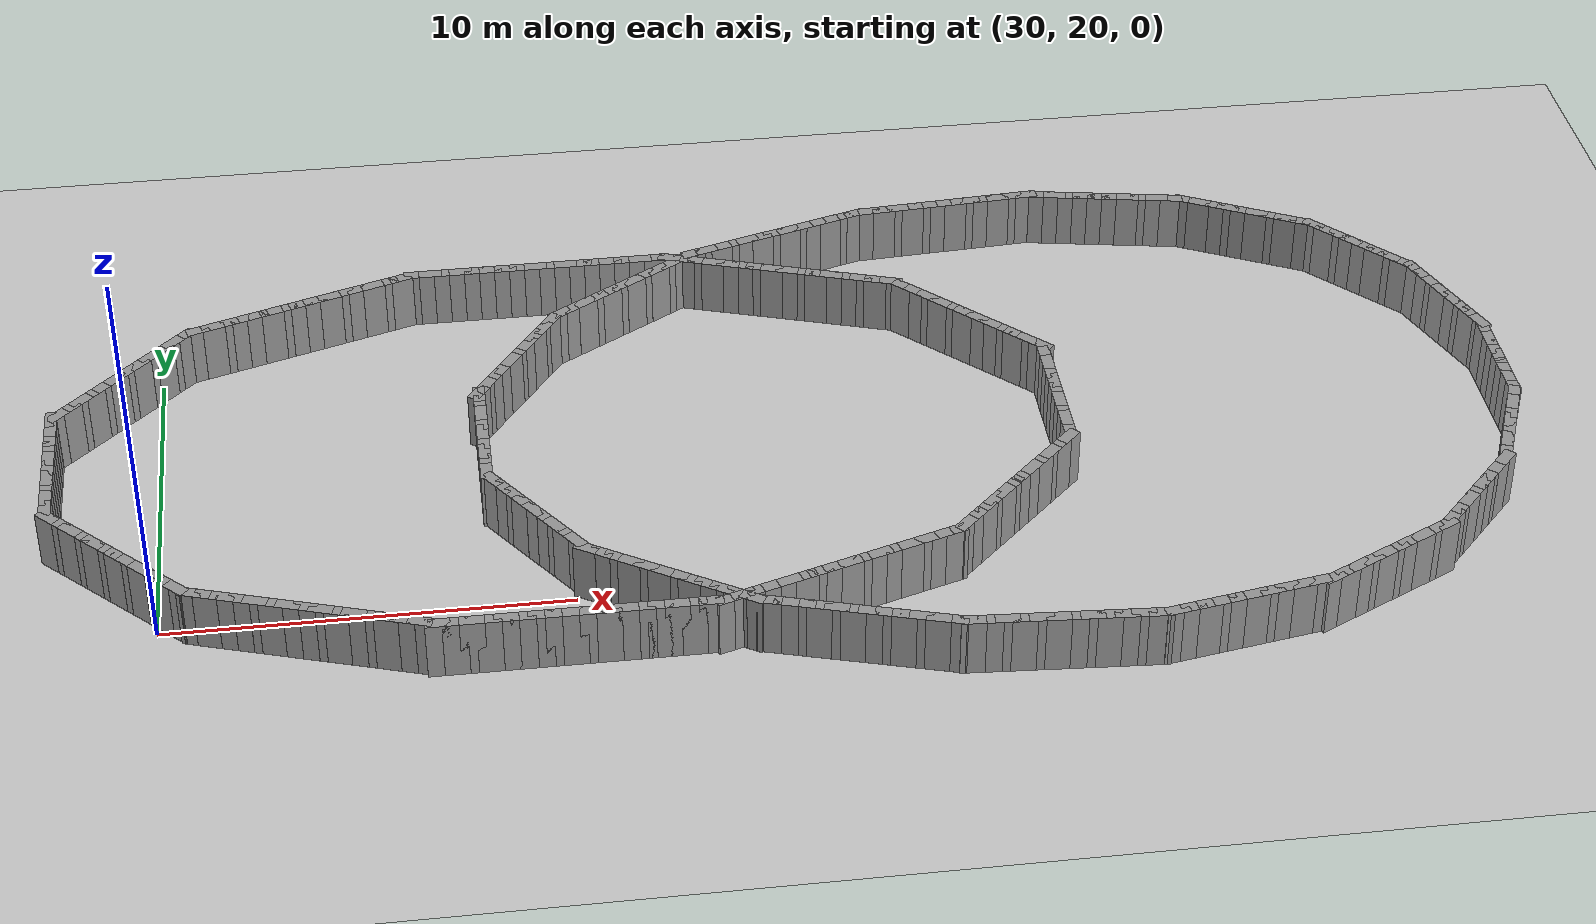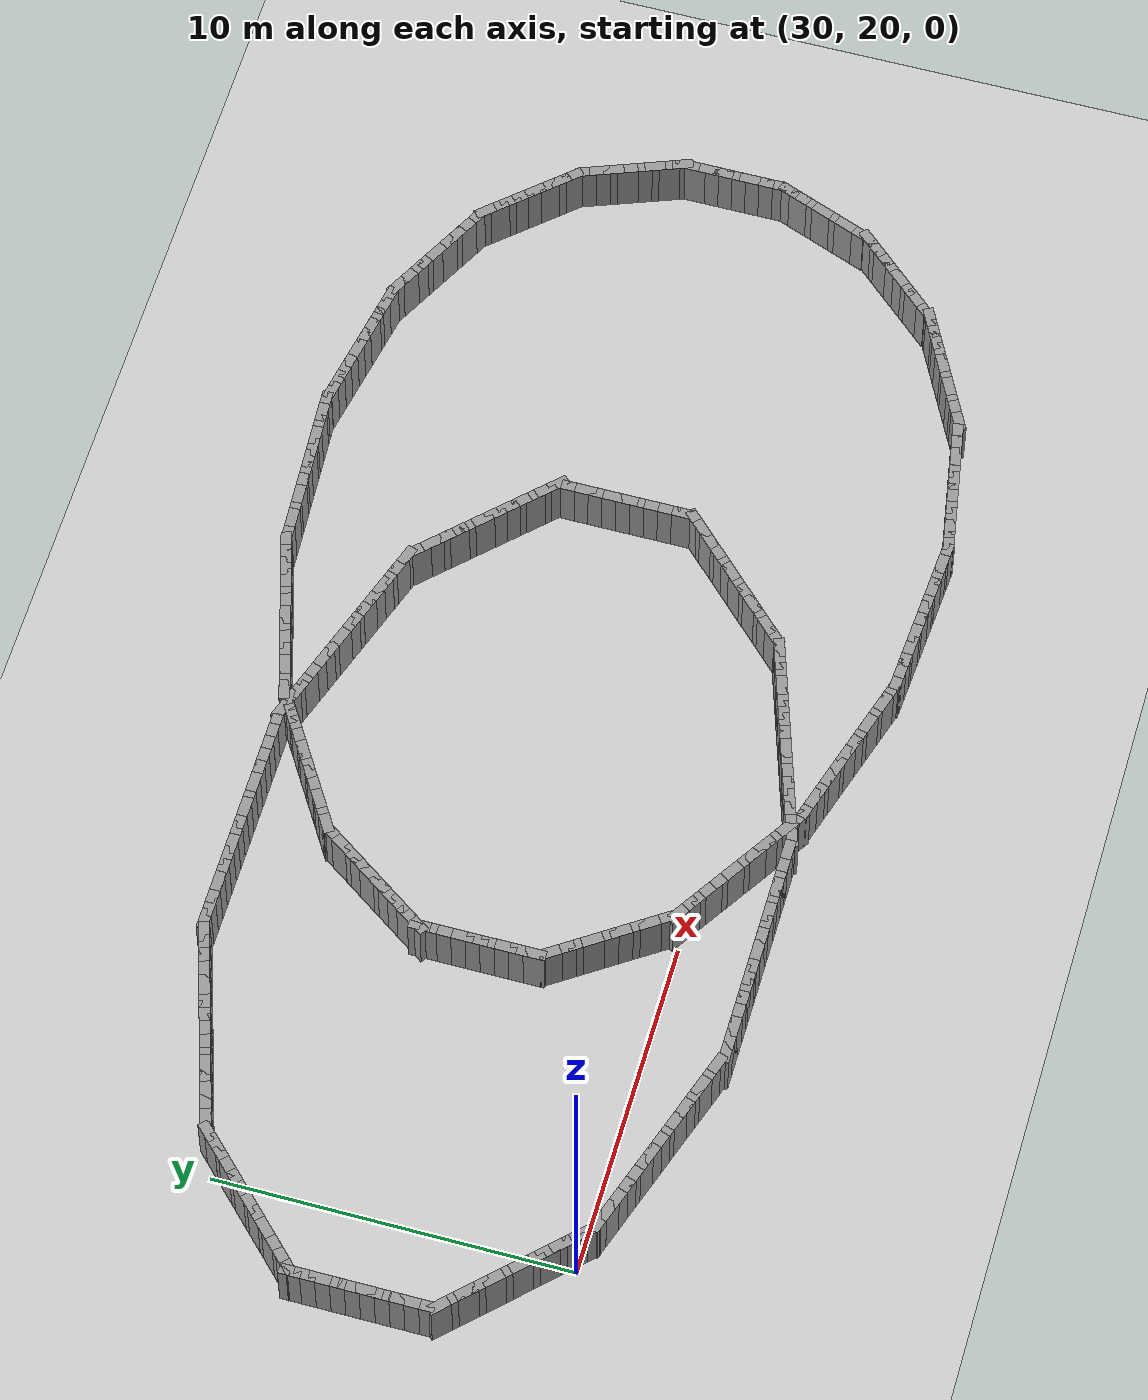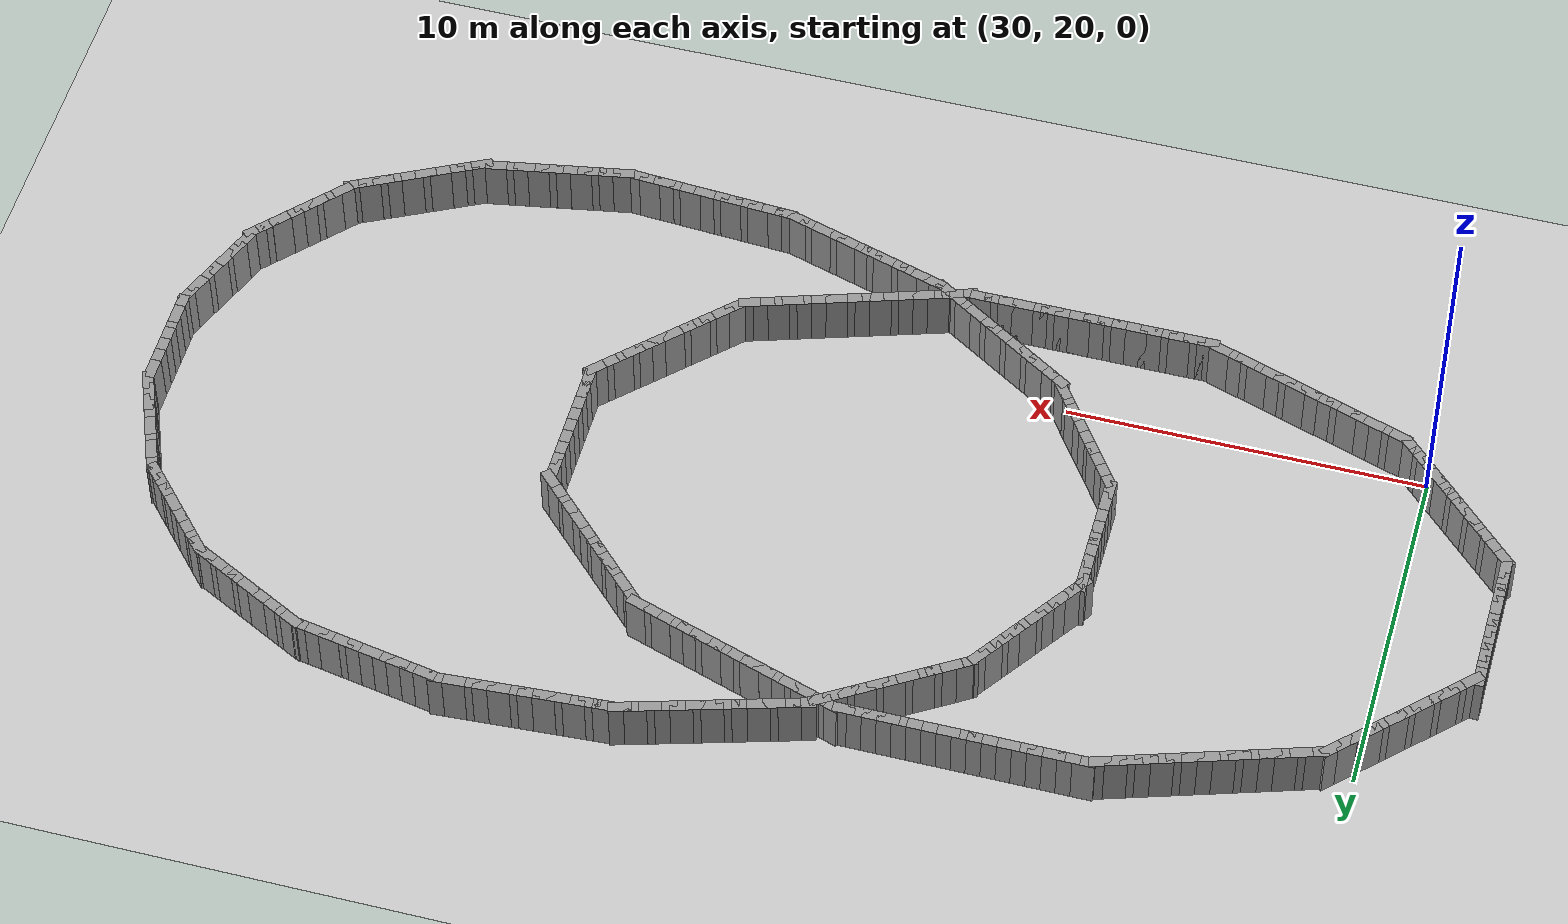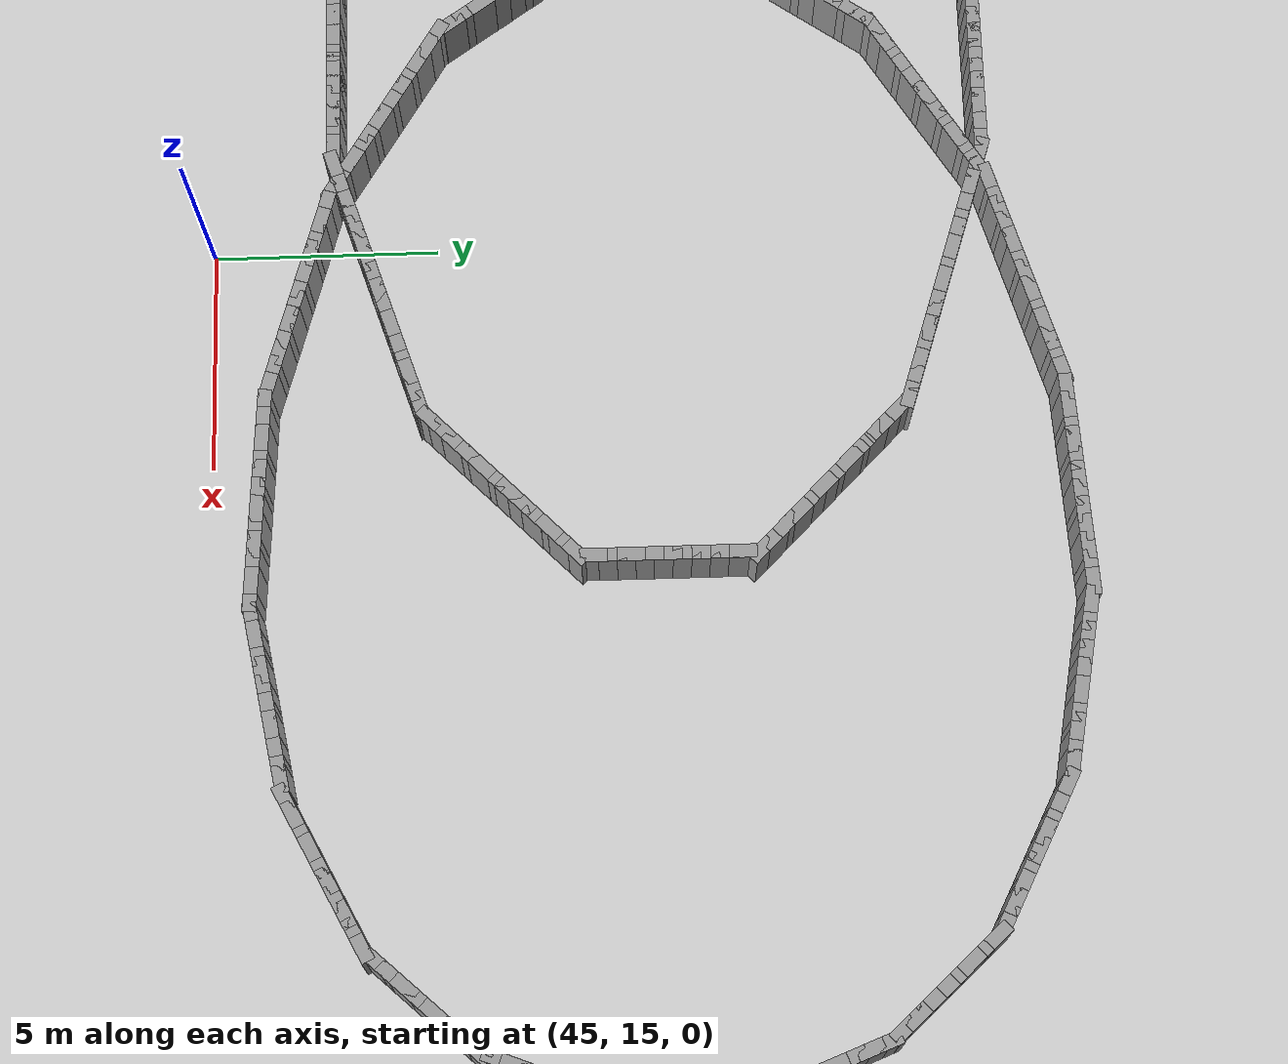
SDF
<?xml version="1.0" ?>
<sdf version="1.5">
  <world name="test_variable_width">
    <include><uri>model://sun</uri></include>
    <include><uri>model://ground_plane</uri></include>
    <model name="curbL_0">
      <static>true</static>
      <pose>27.376 26.938 0.750 0 0 -1.571</pose>
      <link name="link">
        <collision name="col">
          <geometry><box><size>0.600 0.300 1.500</size></box></geometry>
        </collision>
        <visual name="vis">
          <geometry><box><size>0.600 0.300 1.500</size></box></geometry>
          <material>
            <ambient>0.6 0.6 0.6 1</ambient>
            <diffuse>0.6 0.6 0.6 1</diffuse>
          </material>
        </visual>
      </link>
    </model>
    <model name="curbL_1">
      <static>true</static>
      <pose>27.376 26.538 0.750 0 0 -1.571</pose>
      <link name="link">
        <collision name="col">
          <geometry><box><size>0.600 0.300 1.500</size></box></geometry>
        </collision>
        <visual name="vis">
          <geometry><box><size>0.600 0.300 1.500</size></box></geometry>
          <material>
            <ambient>0.6 0.6 0.6 1</ambient>
            <diffuse>0.6 0.6 0.6 1</diffuse>
          </material>
        </visual>
      </link>
    </model>
    <model name="curbL_2">
      <static>true</static>
      <pose>27.376 26.138 0.750 0 0 -1.571</pose>
      <link name="link">
        <collision name="col">
          <geometry><box><size>0.600 0.300 1.500</size></box></geometry>
        </collision>
        <visual name="vis">
          <geometry><box><size>0.600 0.300 1.500</size></box></geometry>
          <material>
            <ambient>0.6 0.6 0.6 1</ambient>
            <diffuse>0.6 0.6 0.6 1</diffuse>
          </material>
        </visual>
      </link>
    </model>
    <model name="curbL_3">
      <static>true</static>
      <pose>27.376 25.738 0.750 0 0 -1.571</pose>
      <link name="link">
        <collision name="col">
          <geometry><box><size>0.600 0.300 1.500</size></box></geometry>
        </collision>
        <visual name="vis">
          <geometry><box><size>0.600 0.300 1.500</size></box></geometry>
          <material>
            <ambient>0.6 0.6 0.6 1</ambient>
            <diffuse>0.6 0.6 0.6 1</diffuse>
          </material>
        </visual>
      </link>
    </model>
    <model name="curbL_4">
      <static>true</static>
      <pose>27.376 25.338 0.750 0 0 -1.571</pose>
      <link name="link">
        <collision name="col">
          <geometry><box><size>0.600 0.300 1.500</size></box></geometry>
        </collision>
        <visual name="vis">
          <geometry><box><size>0.600 0.300 1.500</size></box></geometry>
          <material>
            <ambient>0.6 0.6 0.6 1</ambient>
            <diffuse>0.6 0.6 0.6 1</diffuse>
          </material>
        </visual>
      </link>
    </model>
    <model name="curbL_5">
      <static>true</static>
      <pose>27.376 24.938 0.750 0 0 -1.571</pose>
      <link name="link">
        <collision name="col">
          <geometry><box><size>0.600 0.300 1.500</size></box></geometry>
        </collision>
        <visual name="vis">
          <geometry><box><size>0.600 0.300 1.500</size></box></geometry>
          <material>
            <ambient>0.6 0.6 0.6 1</ambient>
            <diffuse>0.6 0.6 0.6 1</diffuse>
          </material>
        </visual>
      </link>
    </model>
    <model name="curbL_6">
      <static>true</static>
      <pose>27.376 24.538 0.750 0 0 -1.571</pose>
      <link name="link">
        <collision name="col">
          <geometry><box><size>0.600 0.300 1.500</size></box></geometry>
        </collision>
        <visual name="vis">
          <geometry><box><size>0.600 0.300 1.500</size></box></geometry>
          <material>
            <ambient>0.6 0.6 0.6 1</ambient>
            <diffuse>0.6 0.6 0.6 1</diffuse>
          </material>
        </visual>
      </link>
    </model>
    <model name="curbL_7">
      <static>true</static>
      <pose>27.376 24.138 0.750 0 0 -1.571</pose>
      <link name="link">
        <collision name="col">
          <geometry><box><size>0.600 0.300 1.500</size></box></geometry>
        </collision>
        <visual name="vis">
          <geometry><box><size>0.600 0.300 1.500</size></box></geometry>
          <material>
            <ambient>0.6 0.6 0.6 1</ambient>
            <diffuse>0.6 0.6 0.6 1</diffuse>
          </material>
        </visual>
      </link>
    </model>
    <model name="curbL_8">
      <static>true</static>
      <pose>27.376 23.738 0.750 0 0 -1.571</pose>
      <link name="link">
        <collision name="col">
          <geometry><box><size>0.600 0.300 1.500</size></box></geometry>
        </collision>
        <visual name="vis">
          <geometry><box><size>0.600 0.300 1.500</size></box></geometry>
          <material>
            <ambient>0.6 0.6 0.6 1</ambient>
            <diffuse>0.6 0.6 0.6 1</diffuse>
          </material>
        </visual>
      </link>
    </model>
    <model name="curbL_9">
      <static>true</static>
      <pose>27.376 23.338 0.750 0 0 -1.571</pose>
      <link name="link">
        <collision name="col">
          <geometry><box><size>0.600 0.300 1.500</size></box></geometry>
        </collision>
        <visual name="vis">
          <geometry><box><size>0.600 0.300 1.500</size></box></geometry>
          <material>
            <ambient>0.6 0.6 0.6 1</ambient>
            <diffuse>0.6 0.6 0.6 1</diffuse>
          </material>
        </visual>
      </link>
    </model>
    <model name="curbL_10">
      <static>true</static>
      <pose>27.464 22.974 0.750 0 0 -0.784</pose>
      <link name="link">
        <collision name="col">
          <geometry><box><size>0.600 0.300 1.500</size></box></geometry>
        </collision>
        <visual name="vis">
          <geometry><box><size>0.600 0.300 1.500</size></box></geometry>
          <material>
            <ambient>0.6 0.6 0.6 1</ambient>
            <diffuse>0.6 0.6 0.6 1</diffuse>
          </material>
        </visual>
      </link>
    </model>
    <model name="curbL_11">
      <static>true</static>
      <pose>27.748 22.692 0.750 0 0 -0.784</pose>
      <link name="link">
        <collision name="col">
          <geometry><box><size>0.600 0.300 1.500</size></box></geometry>
        </collision>
        <visual name="vis">
          <geometry><box><size>0.600 0.300 1.500</size></box></geometry>
          <material>
            <ambient>0.6 0.6 0.6 1</ambient>
            <diffuse>0.6 0.6 0.6 1</diffuse>
          </material>
        </visual>
      </link>
    </model>
    <model name="curbL_12">
      <static>true</static>
      <pose>28.031 22.409 0.750 0 0 -0.784</pose>
      <link name="link">
        <collision name="col">
          <geometry><box><size>0.600 0.300 1.500</size></box></geometry>
        </collision>
        <visual name="vis">
          <geometry><box><size>0.600 0.300 1.500</size></box></geometry>
          <material>
            <ambient>0.6 0.6 0.6 1</ambient>
            <diffuse>0.6 0.6 0.6 1</diffuse>
          </material>
        </visual>
      </link>
    </model>
    <model name="curbL_13">
      <static>true</static>
      <pose>28.314 22.127 0.750 0 0 -0.784</pose>
      <link name="link">
        <collision name="col">
          <geometry><box><size>0.600 0.300 1.500</size></box></geometry>
        </collision>
        <visual name="vis">
          <geometry><box><size>0.600 0.300 1.500</size></box></geometry>
          <material>
            <ambient>0.6 0.6 0.6 1</ambient>
            <diffuse>0.6 0.6 0.6 1</diffuse>
          </material>
        </visual>
      </link>
    </model>
    <model name="curbL_14">
      <static>true</static>
      <pose>28.597 21.844 0.750 0 0 -0.784</pose>
      <link name="link">
        <collision name="col">
          <geometry><box><size>0.600 0.300 1.500</size></box></geometry>
        </collision>
        <visual name="vis">
          <geometry><box><size>0.600 0.300 1.500</size></box></geometry>
          <material>
            <ambient>0.6 0.6 0.6 1</ambient>
            <diffuse>0.6 0.6 0.6 1</diffuse>
          </material>
        </visual>
      </link>
    </model>
    <model name="curbL_15">
      <static>true</static>
      <pose>28.880 21.562 0.750 0 0 -0.784</pose>
      <link name="link">
        <collision name="col">
          <geometry><box><size>0.600 0.300 1.500</size></box></geometry>
        </collision>
        <visual name="vis">
          <geometry><box><size>0.600 0.300 1.500</size></box></geometry>
          <material>
            <ambient>0.6 0.6 0.6 1</ambient>
            <diffuse>0.6 0.6 0.6 1</diffuse>
          </material>
        </visual>
      </link>
    </model>
    <model name="curbL_16">
      <static>true</static>
      <pose>29.163 21.279 0.750 0 0 -0.784</pose>
      <link name="link">
        <collision name="col">
          <geometry><box><size>0.600 0.300 1.500</size></box></geometry>
        </collision>
        <visual name="vis">
          <geometry><box><size>0.600 0.300 1.500</size></box></geometry>
          <material>
            <ambient>0.6 0.6 0.6 1</ambient>
            <diffuse>0.6 0.6 0.6 1</diffuse>
          </material>
        </visual>
      </link>
    </model>
    <model name="curbL_17">
      <static>true</static>
      <pose>29.447 20.997 0.750 0 0 -0.784</pose>
      <link name="link">
        <collision name="col">
          <geometry><box><size>0.600 0.300 1.500</size></box></geometry>
        </collision>
        <visual name="vis">
          <geometry><box><size>0.600 0.300 1.500</size></box></geometry>
          <material>
            <ambient>0.6 0.6 0.6 1</ambient>
            <diffuse>0.6 0.6 0.6 1</diffuse>
          </material>
        </visual>
      </link>
    </model>
    <model name="curbL_18">
      <static>true</static>
      <pose>29.730 20.714 0.750 0 0 -0.784</pose>
      <link name="link">
        <collision name="col">
          <geometry><box><size>0.600 0.300 1.500</size></box></geometry>
        </collision>
        <visual name="vis">
          <geometry><box><size>0.600 0.300 1.500</size></box></geometry>
          <material>
            <ambient>0.6 0.6 0.6 1</ambient>
            <diffuse>0.6 0.6 0.6 1</diffuse>
          </material>
        </visual>
      </link>
    </model>
    <model name="curbL_19">
      <static>true</static>
      <pose>30.013 20.432 0.750 0 0 -0.784</pose>
      <link name="link">
        <collision name="col">
          <geometry><box><size>0.600 0.300 1.500</size></box></geometry>
        </collision>
        <visual name="vis">
          <geometry><box><size>0.600 0.300 1.500</size></box></geometry>
          <material>
            <ambient>0.6 0.6 0.6 1</ambient>
            <diffuse>0.6 0.6 0.6 1</diffuse>
          </material>
        </visual>
      </link>
    </model>
    <model name="curbL_20">
      <static>true</static>
      <pose>30.296 20.149 0.750 0 0 -0.784</pose>
      <link name="link">
        <collision name="col">
          <geometry><box><size>0.600 0.300 1.500</size></box></geometry>
        </collision>
        <visual name="vis">
          <geometry><box><size>0.600 0.300 1.500</size></box></geometry>
          <material>
            <ambient>0.6 0.6 0.6 1</ambient>
            <diffuse>0.6 0.6 0.6 1</diffuse>
          </material>
        </visual>
      </link>
    </model>
    <model name="curbL_21">
      <static>true</static>
      <pose>30.579 19.867 0.750 0 0 -0.784</pose>
      <link name="link">
        <collision name="col">
          <geometry><box><size>0.600 0.300 1.500</size></box></geometry>
        </collision>
        <visual name="vis">
          <geometry><box><size>0.600 0.300 1.500</size></box></geometry>
          <material>
            <ambient>0.6 0.6 0.6 1</ambient>
            <diffuse>0.6 0.6 0.6 1</diffuse>
          </material>
        </visual>
      </link>
    </model>
    <model name="curbL_22">
      <static>true</static>
      <pose>30.906 19.655 0.750 0 0 -0.316</pose>
      <link name="link">
        <collision name="col">
          <geometry><box><size>0.600 0.300 1.500</size></box></geometry>
        </collision>
        <visual name="vis">
          <geometry><box><size>0.600 0.300 1.500</size></box></geometry>
          <material>
            <ambient>0.6 0.6 0.6 1</ambient>
            <diffuse>0.6 0.6 0.6 1</diffuse>
          </material>
        </visual>
      </link>
    </model>
    <model name="curbL_23">
      <static>true</static>
      <pose>31.286 19.530 0.750 0 0 -0.316</pose>
      <link name="link">
        <collision name="col">
          <geometry><box><size>0.600 0.300 1.500</size></box></geometry>
        </collision>
        <visual name="vis">
          <geometry><box><size>0.600 0.300 1.500</size></box></geometry>
          <material>
            <ambient>0.6 0.6 0.6 1</ambient>
            <diffuse>0.6 0.6 0.6 1</diffuse>
          </material>
        </visual>
      </link>
    </model>
    <model name="curbL_24">
      <static>true</static>
      <pose>31.666 19.406 0.750 0 0 -0.316</pose>
      <link name="link">
        <collision name="col">
          <geometry><box><size>0.600 0.300 1.500</size></box></geometry>
        </collision>
        <visual name="vis">
          <geometry><box><size>0.600 0.300 1.500</size></box></geometry>
          <material>
            <ambient>0.6 0.6 0.6 1</ambient>
            <diffuse>0.6 0.6 0.6 1</diffuse>
          </material>
        </visual>
      </link>
    </model>
    <model name="curbL_25">
      <static>true</static>
      <pose>32.046 19.282 0.750 0 0 -0.316</pose>
      <link name="link">
        <collision name="col">
          <geometry><box><size>0.600 0.300 1.500</size></box></geometry>
        </collision>
        <visual name="vis">
          <geometry><box><size>0.600 0.300 1.500</size></box></geometry>
          <material>
            <ambient>0.6 0.6 0.6 1</ambient>
            <diffuse>0.6 0.6 0.6 1</diffuse>
          </material>
        </visual>
      </link>
    </model>
    <model name="curbL_26">
      <static>true</static>
      <pose>32.426 19.158 0.750 0 0 -0.316</pose>
      <link name="link">
        <collision name="col">
          <geometry><box><size>0.600 0.300 1.500</size></box></geometry>
        </collision>
        <visual name="vis">
          <geometry><box><size>0.600 0.300 1.500</size></box></geometry>
          <material>
            <ambient>0.6 0.6 0.6 1</ambient>
            <diffuse>0.6 0.6 0.6 1</diffuse>
          </material>
        </visual>
      </link>
    </model>
    <model name="curbL_27">
      <static>true</static>
      <pose>32.807 19.033 0.750 0 0 -0.316</pose>
      <link name="link">
        <collision name="col">
          <geometry><box><size>0.600 0.300 1.500</size></box></geometry>
        </collision>
        <visual name="vis">
          <geometry><box><size>0.600 0.300 1.500</size></box></geometry>
          <material>
            <ambient>0.6 0.6 0.6 1</ambient>
            <diffuse>0.6 0.6 0.6 1</diffuse>
          </material>
        </visual>
      </link>
    </model>
    <model name="curbL_28">
      <static>true</static>
      <pose>33.187 18.909 0.750 0 0 -0.316</pose>
      <link name="link">
        <collision name="col">
          <geometry><box><size>0.600 0.300 1.500</size></box></geometry>
        </collision>
        <visual name="vis">
          <geometry><box><size>0.600 0.300 1.500</size></box></geometry>
          <material>
            <ambient>0.6 0.6 0.6 1</ambient>
            <diffuse>0.6 0.6 0.6 1</diffuse>
          </material>
        </visual>
      </link>
    </model>
    <model name="curbL_29">
      <static>true</static>
      <pose>33.567 18.785 0.750 0 0 -0.316</pose>
      <link name="link">
        <collision name="col">
          <geometry><box><size>0.600 0.300 1.500</size></box></geometry>
        </collision>
        <visual name="vis">
          <geometry><box><size>0.600 0.300 1.500</size></box></geometry>
          <material>
            <ambient>0.6 0.6 0.6 1</ambient>
            <diffuse>0.6 0.6 0.6 1</diffuse>
          </material>
        </visual>
      </link>
    </model>
    <model name="curbL_30">
      <static>true</static>
      <pose>33.947 18.661 0.750 0 0 -0.316</pose>
      <link name="link">
        <collision name="col">
          <geometry><box><size>0.600 0.300 1.500</size></box></geometry>
        </collision>
        <visual name="vis">
          <geometry><box><size>0.600 0.300 1.500</size></box></geometry>
          <material>
            <ambient>0.6 0.6 0.6 1</ambient>
            <diffuse>0.6 0.6 0.6 1</diffuse>
          </material>
        </visual>
      </link>
    </model>
    <model name="curbL_31">
      <static>true</static>
      <pose>34.328 18.536 0.750 0 0 -0.316</pose>
      <link name="link">
        <collision name="col">
          <geometry><box><size>0.600 0.300 1.500</size></box></geometry>
        </collision>
        <visual name="vis">
          <geometry><box><size>0.600 0.300 1.500</size></box></geometry>
          <material>
            <ambient>0.6 0.6 0.6 1</ambient>
            <diffuse>0.6 0.6 0.6 1</diffuse>
          </material>
        </visual>
      </link>
    </model>
    <model name="curbL_32">
      <static>true</static>
      <pose>34.708 18.412 0.750 0 0 -0.316</pose>
      <link name="link">
        <collision name="col">
          <geometry><box><size>0.600 0.300 1.500</size></box></geometry>
        </collision>
        <visual name="vis">
          <geometry><box><size>0.600 0.300 1.500</size></box></geometry>
          <material>
            <ambient>0.6 0.6 0.6 1</ambient>
            <diffuse>0.6 0.6 0.6 1</diffuse>
          </material>
        </visual>
      </link>
    </model>
    <model name="curbL_33">
      <static>true</static>
      <pose>35.088 18.288 0.750 0 0 -0.316</pose>
      <link name="link">
        <collision name="col">
          <geometry><box><size>0.600 0.300 1.500</size></box></geometry>
        </collision>
        <visual name="vis">
          <geometry><box><size>0.600 0.300 1.500</size></box></geometry>
          <material>
            <ambient>0.6 0.6 0.6 1</ambient>
            <diffuse>0.6 0.6 0.6 1</diffuse>
          </material>
        </visual>
      </link>
    </model>
    <model name="curbL_34">
      <static>true</static>
      <pose>35.468 18.163 0.750 0 0 -0.316</pose>
      <link name="link">
        <collision name="col">
          <geometry><box><size>0.600 0.300 1.500</size></box></geometry>
        </collision>
        <visual name="vis">
          <geometry><box><size>0.600 0.300 1.500</size></box></geometry>
          <material>
            <ambient>0.6 0.6 0.6 1</ambient>
            <diffuse>0.6 0.6 0.6 1</diffuse>
          </material>
        </visual>
      </link>
    </model>
    <model name="curbL_35">
      <static>true</static>
      <pose>35.848 18.039 0.750 0 0 -0.316</pose>
      <link name="link">
        <collision name="col">
          <geometry><box><size>0.600 0.300 1.500</size></box></geometry>
        </collision>
        <visual name="vis">
          <geometry><box><size>0.600 0.300 1.500</size></box></geometry>
          <material>
            <ambient>0.6 0.6 0.6 1</ambient>
            <diffuse>0.6 0.6 0.6 1</diffuse>
          </material>
        </visual>
      </link>
    </model>
    <model name="curbL_36">
      <static>true</static>
      <pose>36.229 17.915 0.750 0 0 -0.316</pose>
      <link name="link">
        <collision name="col">
          <geometry><box><size>0.600 0.300 1.500</size></box></geometry>
        </collision>
        <visual name="vis">
          <geometry><box><size>0.600 0.300 1.500</size></box></geometry>
          <material>
            <ambient>0.6 0.6 0.6 1</ambient>
            <diffuse>0.6 0.6 0.6 1</diffuse>
          </material>
        </visual>
      </link>
    </model>
    <model name="curbL_37">
      <static>true</static>
      <pose>36.609 17.791 0.750 0 0 0.000</pose>
      <link name="link">
        <collision name="col">
          <geometry><box><size>0.600 0.300 1.500</size></box></geometry>
        </collision>
        <visual name="vis">
          <geometry><box><size>0.600 0.300 1.500</size></box></geometry>
          <material>
            <ambient>0.6 0.6 0.6 1</ambient>
            <diffuse>0.6 0.6 0.6 1</diffuse>
          </material>
        </visual>
      </link>
    </model>
    <model name="curbL_38">
      <static>true</static>
      <pose>37.009 17.791 0.750 0 0 0.000</pose>
      <link name="link">
        <collision name="col">
          <geometry><box><size>0.600 0.300 1.500</size></box></geometry>
        </collision>
        <visual name="vis">
          <geometry><box><size>0.600 0.300 1.500</size></box></geometry>
          <material>
            <ambient>0.6 0.6 0.6 1</ambient>
            <diffuse>0.6 0.6 0.6 1</diffuse>
          </material>
        </visual>
      </link>
    </model>
    <model name="curbL_39">
      <static>true</static>
      <pose>37.409 17.791 0.750 0 0 0.000</pose>
      <link name="link">
        <collision name="col">
          <geometry><box><size>0.600 0.300 1.500</size></box></geometry>
        </collision>
        <visual name="vis">
          <geometry><box><size>0.600 0.300 1.500</size></box></geometry>
          <material>
            <ambient>0.6 0.6 0.6 1</ambient>
            <diffuse>0.6 0.6 0.6 1</diffuse>
          </material>
        </visual>
      </link>
    </model>
    <model name="curbL_40">
      <static>true</static>
      <pose>37.809 17.791 0.750 0 0 0.000</pose>
      <link name="link">
        <collision name="col">
          <geometry><box><size>0.600 0.300 1.500</size></box></geometry>
        </collision>
        <visual name="vis">
          <geometry><box><size>0.600 0.300 1.500</size></box></geometry>
          <material>
            <ambient>0.6 0.6 0.6 1</ambient>
            <diffuse>0.6 0.6 0.6 1</diffuse>
          </material>
        </visual>
      </link>
    </model>
    <model name="curbL_41">
      <static>true</static>
      <pose>38.209 17.791 0.750 0 0 0.000</pose>
      <link name="link">
        <collision name="col">
          <geometry><box><size>0.600 0.300 1.500</size></box></geometry>
        </collision>
        <visual name="vis">
          <geometry><box><size>0.600 0.300 1.500</size></box></geometry>
          <material>
            <ambient>0.6 0.6 0.6 1</ambient>
            <diffuse>0.6 0.6 0.6 1</diffuse>
          </material>
        </visual>
      </link>
    </model>
    <model name="curbL_42">
      <static>true</static>
      <pose>38.609 17.791 0.750 0 0 0.000</pose>
      <link name="link">
        <collision name="col">
          <geometry><box><size>0.600 0.300 1.500</size></box></geometry>
        </collision>
        <visual name="vis">
          <geometry><box><size>0.600 0.300 1.500</size></box></geometry>
          <material>
            <ambient>0.6 0.6 0.6 1</ambient>
            <diffuse>0.6 0.6 0.6 1</diffuse>
          </material>
        </visual>
      </link>
    </model>
    <model name="curbL_43">
      <static>true</static>
      <pose>39.009 17.791 0.750 0 0 0.000</pose>
      <link name="link">
        <collision name="col">
          <geometry><box><size>0.600 0.300 1.500</size></box></geometry>
        </collision>
        <visual name="vis">
          <geometry><box><size>0.600 0.300 1.500</size></box></geometry>
          <material>
            <ambient>0.6 0.6 0.6 1</ambient>
            <diffuse>0.6 0.6 0.6 1</diffuse>
          </material>
        </visual>
      </link>
    </model>
    <model name="curbL_44">
      <static>true</static>
      <pose>39.409 17.791 0.750 0 0 0.000</pose>
      <link name="link">
        <collision name="col">
          <geometry><box><size>0.600 0.300 1.500</size></box></geometry>
        </collision>
        <visual name="vis">
          <geometry><box><size>0.600 0.300 1.500</size></box></geometry>
          <material>
            <ambient>0.6 0.6 0.6 1</ambient>
            <diffuse>0.6 0.6 0.6 1</diffuse>
          </material>
        </visual>
      </link>
    </model>
    <model name="curbL_45">
      <static>true</static>
      <pose>39.809 17.791 0.750 0 0 0.000</pose>
      <link name="link">
        <collision name="col">
          <geometry><box><size>0.600 0.300 1.500</size></box></geometry>
        </collision>
        <visual name="vis">
          <geometry><box><size>0.600 0.300 1.500</size></box></geometry>
          <material>
            <ambient>0.6 0.6 0.6 1</ambient>
            <diffuse>0.6 0.6 0.6 1</diffuse>
          </material>
        </visual>
      </link>
    </model>
    <model name="curbL_46">
      <static>true</static>
      <pose>40.209 17.791 0.750 0 0 0.000</pose>
      <link name="link">
        <collision name="col">
          <geometry><box><size>0.600 0.300 1.500</size></box></geometry>
        </collision>
        <visual name="vis">
          <geometry><box><size>0.600 0.300 1.500</size></box></geometry>
          <material>
            <ambient>0.6 0.6 0.6 1</ambient>
            <diffuse>0.6 0.6 0.6 1</diffuse>
          </material>
        </visual>
      </link>
    </model>
    <model name="curbL_47">
      <static>true</static>
      <pose>40.609 17.791 0.750 0 0 0.000</pose>
      <link name="link">
        <collision name="col">
          <geometry><box><size>0.600 0.300 1.500</size></box></geometry>
        </collision>
        <visual name="vis">
          <geometry><box><size>0.600 0.300 1.500</size></box></geometry>
          <material>
            <ambient>0.6 0.6 0.6 1</ambient>
            <diffuse>0.6 0.6 0.6 1</diffuse>
          </material>
        </visual>
      </link>
    </model>
    <model name="curbL_48">
      <static>true</static>
      <pose>41.009 17.791 0.750 0 0 0.000</pose>
      <link name="link">
        <collision name="col">
          <geometry><box><size>0.600 0.300 1.500</size></box></geometry>
        </collision>
        <visual name="vis">
          <geometry><box><size>0.600 0.300 1.500</size></box></geometry>
          <material>
            <ambient>0.6 0.6 0.6 1</ambient>
            <diffuse>0.6 0.6 0.6 1</diffuse>
          </material>
        </visual>
      </link>
    </model>
    <model name="curbL_49">
      <static>true</static>
      <pose>41.409 17.791 0.750 0 0 0.000</pose>
      <link name="link">
        <collision name="col">
          <geometry><box><size>0.600 0.300 1.500</size></box></geometry>
        </collision>
        <visual name="vis">
          <geometry><box><size>0.600 0.300 1.500</size></box></geometry>
          <material>
            <ambient>0.6 0.6 0.6 1</ambient>
            <diffuse>0.6 0.6 0.6 1</diffuse>
          </material>
        </visual>
      </link>
    </model>
    <model name="curbL_50">
      <static>true</static>
      <pose>41.809 17.791 0.750 0 0 0.000</pose>
      <link name="link">
        <collision name="col">
          <geometry><box><size>0.600 0.300 1.500</size></box></geometry>
        </collision>
        <visual name="vis">
          <geometry><box><size>0.600 0.300 1.500</size></box></geometry>
          <material>
            <ambient>0.6 0.6 0.6 1</ambient>
            <diffuse>0.6 0.6 0.6 1</diffuse>
          </material>
        </visual>
      </link>
    </model>
    <model name="curbL_51">
      <static>true</static>
      <pose>42.209 17.791 0.750 0 0 0.000</pose>
      <link name="link">
        <collision name="col">
          <geometry><box><size>0.600 0.300 1.500</size></box></geometry>
        </collision>
        <visual name="vis">
          <geometry><box><size>0.600 0.300 1.500</size></box></geometry>
          <material>
            <ambient>0.6 0.6 0.6 1</ambient>
            <diffuse>0.6 0.6 0.6 1</diffuse>
          </material>
        </visual>
      </link>
    </model>
    <model name="curbL_52">
      <static>true</static>
      <pose>42.609 17.791 0.750 0 0 0.000</pose>
      <link name="link">
        <collision name="col">
          <geometry><box><size>0.600 0.300 1.500</size></box></geometry>
        </collision>
        <visual name="vis">
          <geometry><box><size>0.600 0.300 1.500</size></box></geometry>
          <material>
            <ambient>0.6 0.6 0.6 1</ambient>
            <diffuse>0.6 0.6 0.6 1</diffuse>
          </material>
        </visual>
      </link>
    </model>
    <model name="curbL_53">
      <static>true</static>
      <pose>43.009 17.791 0.750 0 0 0.000</pose>
      <link name="link">
        <collision name="col">
          <geometry><box><size>0.600 0.300 1.500</size></box></geometry>
        </collision>
        <visual name="vis">
          <geometry><box><size>0.600 0.300 1.500</size></box></geometry>
          <material>
            <ambient>0.6 0.6 0.6 1</ambient>
            <diffuse>0.6 0.6 0.6 1</diffuse>
          </material>
        </visual>
      </link>
    </model>
    <model name="curbL_54">
      <static>true</static>
      <pose>43.408 17.796 0.750 0 0 0.316</pose>
      <link name="link">
        <collision name="col">
          <geometry><box><size>0.600 0.300 1.500</size></box></geometry>
        </collision>
        <visual name="vis">
          <geometry><box><size>0.600 0.300 1.500</size></box></geometry>
          <material>
            <ambient>0.6 0.6 0.6 1</ambient>
            <diffuse>0.6 0.6 0.6 1</diffuse>
          </material>
        </visual>
      </link>
    </model>
    <model name="curbL_55">
      <static>true</static>
      <pose>43.788 17.920 0.750 0 0 0.316</pose>
      <link name="link">
        <collision name="col">
          <geometry><box><size>0.600 0.300 1.500</size></box></geometry>
        </collision>
        <visual name="vis">
          <geometry><box><size>0.600 0.300 1.500</size></box></geometry>
          <material>
            <ambient>0.6 0.6 0.6 1</ambient>
            <diffuse>0.6 0.6 0.6 1</diffuse>
          </material>
        </visual>
      </link>
    </model>
    <model name="curbL_56">
      <static>true</static>
      <pose>44.169 18.045 0.750 0 0 0.316</pose>
      <link name="link">
        <collision name="col">
          <geometry><box><size>0.600 0.300 1.500</size></box></geometry>
        </collision>
        <visual name="vis">
          <geometry><box><size>0.600 0.300 1.500</size></box></geometry>
          <material>
            <ambient>0.6 0.6 0.6 1</ambient>
            <diffuse>0.6 0.6 0.6 1</diffuse>
          </material>
        </visual>
      </link>
    </model>
    <model name="curbL_57">
      <static>true</static>
      <pose>44.549 18.169 0.750 0 0 0.316</pose>
      <link name="link">
        <collision name="col">
          <geometry><box><size>0.600 0.300 1.500</size></box></geometry>
        </collision>
        <visual name="vis">
          <geometry><box><size>0.600 0.300 1.500</size></box></geometry>
          <material>
            <ambient>0.6 0.6 0.6 1</ambient>
            <diffuse>0.6 0.6 0.6 1</diffuse>
          </material>
        </visual>
      </link>
    </model>
    <model name="curbL_58">
      <static>true</static>
      <pose>44.929 18.293 0.750 0 0 0.316</pose>
      <link name="link">
        <collision name="col">
          <geometry><box><size>0.600 0.300 1.500</size></box></geometry>
        </collision>
        <visual name="vis">
          <geometry><box><size>0.600 0.300 1.500</size></box></geometry>
          <material>
            <ambient>0.6 0.6 0.6 1</ambient>
            <diffuse>0.6 0.6 0.6 1</diffuse>
          </material>
        </visual>
      </link>
    </model>
    <model name="curbL_59">
      <static>true</static>
      <pose>45.309 18.417 0.750 0 0 0.316</pose>
      <link name="link">
        <collision name="col">
          <geometry><box><size>0.600 0.300 1.500</size></box></geometry>
        </collision>
        <visual name="vis">
          <geometry><box><size>0.600 0.300 1.500</size></box></geometry>
          <material>
            <ambient>0.6 0.6 0.6 1</ambient>
            <diffuse>0.6 0.6 0.6 1</diffuse>
          </material>
        </visual>
      </link>
    </model>
    <model name="curbL_60">
      <static>true</static>
      <pose>45.689 18.542 0.750 0 0 0.316</pose>
      <link name="link">
        <collision name="col">
          <geometry><box><size>0.600 0.300 1.500</size></box></geometry>
        </collision>
        <visual name="vis">
          <geometry><box><size>0.600 0.300 1.500</size></box></geometry>
          <material>
            <ambient>0.6 0.6 0.6 1</ambient>
            <diffuse>0.6 0.6 0.6 1</diffuse>
          </material>
        </visual>
      </link>
    </model>
    <model name="curbL_61">
      <static>true</static>
      <pose>46.070 18.666 0.750 0 0 0.316</pose>
      <link name="link">
        <collision name="col">
          <geometry><box><size>0.600 0.300 1.500</size></box></geometry>
        </collision>
        <visual name="vis">
          <geometry><box><size>0.600 0.300 1.500</size></box></geometry>
          <material>
            <ambient>0.6 0.6 0.6 1</ambient>
            <diffuse>0.6 0.6 0.6 1</diffuse>
          </material>
        </visual>
      </link>
    </model>
    <model name="curbL_62">
      <static>true</static>
      <pose>46.450 18.790 0.750 0 0 0.316</pose>
      <link name="link">
        <collision name="col">
          <geometry><box><size>0.600 0.300 1.500</size></box></geometry>
        </collision>
        <visual name="vis">
          <geometry><box><size>0.600 0.300 1.500</size></box></geometry>
          <material>
            <ambient>0.6 0.6 0.6 1</ambient>
            <diffuse>0.6 0.6 0.6 1</diffuse>
          </material>
        </visual>
      </link>
    </model>
    <model name="curbL_63">
      <static>true</static>
      <pose>46.830 18.915 0.750 0 0 0.316</pose>
      <link name="link">
        <collision name="col">
          <geometry><box><size>0.600 0.300 1.500</size></box></geometry>
        </collision>
        <visual name="vis">
          <geometry><box><size>0.600 0.300 1.500</size></box></geometry>
          <material>
            <ambient>0.6 0.6 0.6 1</ambient>
            <diffuse>0.6 0.6 0.6 1</diffuse>
          </material>
        </visual>
      </link>
    </model>
    <model name="curbL_64">
      <static>true</static>
      <pose>47.210 19.039 0.750 0 0 0.316</pose>
      <link name="link">
        <collision name="col">
          <geometry><box><size>0.600 0.300 1.500</size></box></geometry>
        </collision>
        <visual name="vis">
          <geometry><box><size>0.600 0.300 1.500</size></box></geometry>
          <material>
            <ambient>0.6 0.6 0.6 1</ambient>
            <diffuse>0.6 0.6 0.6 1</diffuse>
          </material>
        </visual>
      </link>
    </model>
    <model name="curbL_65">
      <static>true</static>
      <pose>47.590 19.163 0.750 0 0 0.316</pose>
      <link name="link">
        <collision name="col">
          <geometry><box><size>0.600 0.300 1.500</size></box></geometry>
        </collision>
        <visual name="vis">
          <geometry><box><size>0.600 0.300 1.500</size></box></geometry>
          <material>
            <ambient>0.6 0.6 0.6 1</ambient>
            <diffuse>0.6 0.6 0.6 1</diffuse>
          </material>
        </visual>
      </link>
    </model>
    <model name="curbL_66">
      <static>true</static>
      <pose>47.971 19.287 0.750 0 0 0.316</pose>
      <link name="link">
        <collision name="col">
          <geometry><box><size>0.600 0.300 1.500</size></box></geometry>
        </collision>
        <visual name="vis">
          <geometry><box><size>0.600 0.300 1.500</size></box></geometry>
          <material>
            <ambient>0.6 0.6 0.6 1</ambient>
            <diffuse>0.6 0.6 0.6 1</diffuse>
          </material>
        </visual>
      </link>
    </model>
    <model name="curbL_67">
      <static>true</static>
      <pose>48.351 19.412 0.750 0 0 0.316</pose>
      <link name="link">
        <collision name="col">
          <geometry><box><size>0.600 0.300 1.500</size></box></geometry>
        </collision>
        <visual name="vis">
          <geometry><box><size>0.600 0.300 1.500</size></box></geometry>
          <material>
            <ambient>0.6 0.6 0.6 1</ambient>
            <diffuse>0.6 0.6 0.6 1</diffuse>
          </material>
        </visual>
      </link>
    </model>
    <model name="curbL_68">
      <static>true</static>
      <pose>48.731 19.536 0.750 0 0 0.316</pose>
      <link name="link">
        <collision name="col">
          <geometry><box><size>0.600 0.300 1.500</size></box></geometry>
        </collision>
        <visual name="vis">
          <geometry><box><size>0.600 0.300 1.500</size></box></geometry>
          <material>
            <ambient>0.6 0.6 0.6 1</ambient>
            <diffuse>0.6 0.6 0.6 1</diffuse>
          </material>
        </visual>
      </link>
    </model>
    <model name="curbL_69">
      <static>true</static>
      <pose>49.111 19.660 0.750 0 0 0.316</pose>
      <link name="link">
        <collision name="col">
          <geometry><box><size>0.600 0.300 1.500</size></box></geometry>
        </collision>
        <visual name="vis">
          <geometry><box><size>0.600 0.300 1.500</size></box></geometry>
          <material>
            <ambient>0.6 0.6 0.6 1</ambient>
            <diffuse>0.6 0.6 0.6 1</diffuse>
          </material>
        </visual>
      </link>
    </model>
    <model name="curbL_70">
      <static>true</static>
      <pose>49.433 19.879 0.750 0 0 0.784</pose>
      <link name="link">
        <collision name="col">
          <geometry><box><size>0.600 0.300 1.500</size></box></geometry>
        </collision>
        <visual name="vis">
          <geometry><box><size>0.600 0.300 1.500</size></box></geometry>
          <material>
            <ambient>0.6 0.6 0.6 1</ambient>
            <diffuse>0.6 0.6 0.6 1</diffuse>
          </material>
        </visual>
      </link>
    </model>
    <model name="curbL_71">
      <static>true</static>
      <pose>49.717 20.162 0.750 0 0 0.784</pose>
      <link name="link">
        <collision name="col">
          <geometry><box><size>0.600 0.300 1.500</size></box></geometry>
        </collision>
        <visual name="vis">
          <geometry><box><size>0.600 0.300 1.500</size></box></geometry>
          <material>
            <ambient>0.6 0.6 0.6 1</ambient>
            <diffuse>0.6 0.6 0.6 1</diffuse>
          </material>
        </visual>
      </link>
    </model>
    <model name="curbL_72">
      <static>true</static>
      <pose>50.000 20.444 0.750 0 0 0.784</pose>
      <link name="link">
        <collision name="col">
          <geometry><box><size>0.600 0.300 1.500</size></box></geometry>
        </collision>
        <visual name="vis">
          <geometry><box><size>0.600 0.300 1.500</size></box></geometry>
          <material>
            <ambient>0.6 0.6 0.6 1</ambient>
            <diffuse>0.6 0.6 0.6 1</diffuse>
          </material>
        </visual>
      </link>
    </model>
    <model name="curbL_73">
      <static>true</static>
      <pose>50.283 20.727 0.750 0 0 0.784</pose>
      <link name="link">
        <collision name="col">
          <geometry><box><size>0.600 0.300 1.500</size></box></geometry>
        </collision>
        <visual name="vis">
          <geometry><box><size>0.600 0.300 1.500</size></box></geometry>
          <material>
            <ambient>0.6 0.6 0.6 1</ambient>
            <diffuse>0.6 0.6 0.6 1</diffuse>
          </material>
        </visual>
      </link>
    </model>
    <model name="curbL_74">
      <static>true</static>
      <pose>50.566 21.009 0.750 0 0 0.784</pose>
      <link name="link">
        <collision name="col">
          <geometry><box><size>0.600 0.300 1.500</size></box></geometry>
        </collision>
        <visual name="vis">
          <geometry><box><size>0.600 0.300 1.500</size></box></geometry>
          <material>
            <ambient>0.6 0.6 0.6 1</ambient>
            <diffuse>0.6 0.6 0.6 1</diffuse>
          </material>
        </visual>
      </link>
    </model>
    <model name="curbL_75">
      <static>true</static>
      <pose>50.849 21.292 0.750 0 0 0.784</pose>
      <link name="link">
        <collision name="col">
          <geometry><box><size>0.600 0.300 1.500</size></box></geometry>
        </collision>
        <visual name="vis">
          <geometry><box><size>0.600 0.300 1.500</size></box></geometry>
          <material>
            <ambient>0.6 0.6 0.6 1</ambient>
            <diffuse>0.6 0.6 0.6 1</diffuse>
          </material>
        </visual>
      </link>
    </model>
    <model name="curbL_76">
      <static>true</static>
      <pose>51.132 21.574 0.750 0 0 0.784</pose>
      <link name="link">
        <collision name="col">
          <geometry><box><size>0.600 0.300 1.500</size></box></geometry>
        </collision>
        <visual name="vis">
          <geometry><box><size>0.600 0.300 1.500</size></box></geometry>
          <material>
            <ambient>0.6 0.6 0.6 1</ambient>
            <diffuse>0.6 0.6 0.6 1</diffuse>
          </material>
        </visual>
      </link>
    </model>
    <model name="curbL_77">
      <static>true</static>
      <pose>51.416 21.857 0.750 0 0 0.784</pose>
      <link name="link">
        <collision name="col">
          <geometry><box><size>0.600 0.300 1.500</size></box></geometry>
        </collision>
        <visual name="vis">
          <geometry><box><size>0.600 0.300 1.500</size></box></geometry>
          <material>
            <ambient>0.6 0.6 0.6 1</ambient>
            <diffuse>0.6 0.6 0.6 1</diffuse>
          </material>
        </visual>
      </link>
    </model>
    <model name="curbL_78">
      <static>true</static>
      <pose>51.699 22.139 0.750 0 0 0.784</pose>
      <link name="link">
        <collision name="col">
          <geometry><box><size>0.600 0.300 1.500</size></box></geometry>
        </collision>
        <visual name="vis">
          <geometry><box><size>0.600 0.300 1.500</size></box></geometry>
          <material>
            <ambient>0.6 0.6 0.6 1</ambient>
            <diffuse>0.6 0.6 0.6 1</diffuse>
          </material>
        </visual>
      </link>
    </model>
    <model name="curbL_79">
      <static>true</static>
      <pose>51.982 22.422 0.750 0 0 0.784</pose>
      <link name="link">
        <collision name="col">
          <geometry><box><size>0.600 0.300 1.500</size></box></geometry>
        </collision>
        <visual name="vis">
          <geometry><box><size>0.600 0.300 1.500</size></box></geometry>
          <material>
            <ambient>0.6 0.6 0.6 1</ambient>
            <diffuse>0.6 0.6 0.6 1</diffuse>
          </material>
        </visual>
      </link>
    </model>
    <model name="curbL_80">
      <static>true</static>
      <pose>52.265 22.704 0.750 0 0 0.784</pose>
      <link name="link">
        <collision name="col">
          <geometry><box><size>0.600 0.300 1.500</size></box></geometry>
        </collision>
        <visual name="vis">
          <geometry><box><size>0.600 0.300 1.500</size></box></geometry>
          <material>
            <ambient>0.6 0.6 0.6 1</ambient>
            <diffuse>0.6 0.6 0.6 1</diffuse>
          </material>
        </visual>
      </link>
    </model>
    <model name="curbL_81">
      <static>true</static>
      <pose>52.548 22.987 0.750 0 0 0.784</pose>
      <link name="link">
        <collision name="col">
          <geometry><box><size>0.600 0.300 1.500</size></box></geometry>
        </collision>
        <visual name="vis">
          <geometry><box><size>0.600 0.300 1.500</size></box></geometry>
          <material>
            <ambient>0.6 0.6 0.6 1</ambient>
            <diffuse>0.6 0.6 0.6 1</diffuse>
          </material>
        </visual>
      </link>
    </model>
    <model name="curbL_82">
      <static>true</static>
      <pose>52.624 23.355 0.750 0 0 1.571</pose>
      <link name="link">
        <collision name="col">
          <geometry><box><size>0.600 0.300 1.500</size></box></geometry>
        </collision>
        <visual name="vis">
          <geometry><box><size>0.600 0.300 1.500</size></box></geometry>
          <material>
            <ambient>0.6 0.6 0.6 1</ambient>
            <diffuse>0.6 0.6 0.6 1</diffuse>
          </material>
        </visual>
      </link>
    </model>
    <model name="curbL_83">
      <static>true</static>
      <pose>52.624 23.755 0.750 0 0 1.571</pose>
      <link name="link">
        <collision name="col">
          <geometry><box><size>0.600 0.300 1.500</size></box></geometry>
        </collision>
        <visual name="vis">
          <geometry><box><size>0.600 0.300 1.500</size></box></geometry>
          <material>
            <ambient>0.6 0.6 0.6 1</ambient>
            <diffuse>0.6 0.6 0.6 1</diffuse>
          </material>
        </visual>
      </link>
    </model>
    <model name="curbL_84">
      <static>true</static>
      <pose>52.624 24.155 0.750 0 0 1.571</pose>
      <link name="link">
        <collision name="col">
          <geometry><box><size>0.600 0.300 1.500</size></box></geometry>
        </collision>
        <visual name="vis">
          <geometry><box><size>0.600 0.300 1.500</size></box></geometry>
          <material>
            <ambient>0.6 0.6 0.6 1</ambient>
            <diffuse>0.6 0.6 0.6 1</diffuse>
          </material>
        </visual>
      </link>
    </model>
    <model name="curbL_85">
      <static>true</static>
      <pose>52.624 24.555 0.750 0 0 1.571</pose>
      <link name="link">
        <collision name="col">
          <geometry><box><size>0.600 0.300 1.500</size></box></geometry>
        </collision>
        <visual name="vis">
          <geometry><box><size>0.600 0.300 1.500</size></box></geometry>
          <material>
            <ambient>0.6 0.6 0.6 1</ambient>
            <diffuse>0.6 0.6 0.6 1</diffuse>
          </material>
        </visual>
      </link>
    </model>
    <model name="curbL_86">
      <static>true</static>
      <pose>52.624 24.955 0.750 0 0 1.571</pose>
      <link name="link">
        <collision name="col">
          <geometry><box><size>0.600 0.300 1.500</size></box></geometry>
        </collision>
        <visual name="vis">
          <geometry><box><size>0.600 0.300 1.500</size></box></geometry>
          <material>
            <ambient>0.6 0.6 0.6 1</ambient>
            <diffuse>0.6 0.6 0.6 1</diffuse>
          </material>
        </visual>
      </link>
    </model>
    <model name="curbL_87">
      <static>true</static>
      <pose>52.624 25.355 0.750 0 0 1.571</pose>
      <link name="link">
        <collision name="col">
          <geometry><box><size>0.600 0.300 1.500</size></box></geometry>
        </collision>
        <visual name="vis">
          <geometry><box><size>0.600 0.300 1.500</size></box></geometry>
          <material>
            <ambient>0.6 0.6 0.6 1</ambient>
            <diffuse>0.6 0.6 0.6 1</diffuse>
          </material>
        </visual>
      </link>
    </model>
    <model name="curbL_88">
      <static>true</static>
      <pose>52.624 25.755 0.750 0 0 1.571</pose>
      <link name="link">
        <collision name="col">
          <geometry><box><size>0.600 0.300 1.500</size></box></geometry>
        </collision>
        <visual name="vis">
          <geometry><box><size>0.600 0.300 1.500</size></box></geometry>
          <material>
            <ambient>0.6 0.6 0.6 1</ambient>
            <diffuse>0.6 0.6 0.6 1</diffuse>
          </material>
        </visual>
      </link>
    </model>
    <model name="curbL_89">
      <static>true</static>
      <pose>52.624 26.155 0.750 0 0 1.571</pose>
      <link name="link">
        <collision name="col">
          <geometry><box><size>0.600 0.300 1.500</size></box></geometry>
        </collision>
        <visual name="vis">
          <geometry><box><size>0.600 0.300 1.500</size></box></geometry>
          <material>
            <ambient>0.6 0.6 0.6 1</ambient>
            <diffuse>0.6 0.6 0.6 1</diffuse>
          </material>
        </visual>
      </link>
    </model>
    <model name="curbL_90">
      <static>true</static>
      <pose>52.624 26.555 0.750 0 0 1.571</pose>
      <link name="link">
        <collision name="col">
          <geometry><box><size>0.600 0.300 1.500</size></box></geometry>
        </collision>
        <visual name="vis">
          <geometry><box><size>0.600 0.300 1.500</size></box></geometry>
          <material>
            <ambient>0.6 0.6 0.6 1</ambient>
            <diffuse>0.6 0.6 0.6 1</diffuse>
          </material>
        </visual>
      </link>
    </model>
    <model name="curbL_91">
      <static>true</static>
      <pose>52.611 26.950 0.750 0 0 2.357</pose>
      <link name="link">
        <collision name="col">
          <geometry><box><size>0.600 0.300 1.500</size></box></geometry>
        </collision>
        <visual name="vis">
          <geometry><box><size>0.600 0.300 1.500</size></box></geometry>
          <material>
            <ambient>0.6 0.6 0.6 1</ambient>
            <diffuse>0.6 0.6 0.6 1</diffuse>
          </material>
        </visual>
      </link>
    </model>
    <model name="curbL_92">
      <static>true</static>
      <pose>52.328 27.233 0.750 0 0 2.357</pose>
      <link name="link">
        <collision name="col">
          <geometry><box><size>0.600 0.300 1.500</size></box></geometry>
        </collision>
        <visual name="vis">
          <geometry><box><size>0.600 0.300 1.500</size></box></geometry>
          <material>
            <ambient>0.6 0.6 0.6 1</ambient>
            <diffuse>0.6 0.6 0.6 1</diffuse>
          </material>
        </visual>
      </link>
    </model>
    <model name="curbL_93">
      <static>true</static>
      <pose>52.045 27.515 0.750 0 0 2.357</pose>
      <link name="link">
        <collision name="col">
          <geometry><box><size>0.600 0.300 1.500</size></box></geometry>
        </collision>
        <visual name="vis">
          <geometry><box><size>0.600 0.300 1.500</size></box></geometry>
          <material>
            <ambient>0.6 0.6 0.6 1</ambient>
            <diffuse>0.6 0.6 0.6 1</diffuse>
          </material>
        </visual>
      </link>
    </model>
    <model name="curbL_94">
      <static>true</static>
      <pose>51.762 27.798 0.750 0 0 2.357</pose>
      <link name="link">
        <collision name="col">
          <geometry><box><size>0.600 0.300 1.500</size></box></geometry>
        </collision>
        <visual name="vis">
          <geometry><box><size>0.600 0.300 1.500</size></box></geometry>
          <material>
            <ambient>0.6 0.6 0.6 1</ambient>
            <diffuse>0.6 0.6 0.6 1</diffuse>
          </material>
        </visual>
      </link>
    </model>
    <model name="curbL_95">
      <static>true</static>
      <pose>51.479 28.080 0.750 0 0 2.357</pose>
      <link name="link">
        <collision name="col">
          <geometry><box><size>0.600 0.300 1.500</size></box></geometry>
        </collision>
        <visual name="vis">
          <geometry><box><size>0.600 0.300 1.500</size></box></geometry>
          <material>
            <ambient>0.6 0.6 0.6 1</ambient>
            <diffuse>0.6 0.6 0.6 1</diffuse>
          </material>
        </visual>
      </link>
    </model>
    <model name="curbL_96">
      <static>true</static>
      <pose>51.195 28.363 0.750 0 0 2.357</pose>
      <link name="link">
        <collision name="col">
          <geometry><box><size>0.600 0.300 1.500</size></box></geometry>
        </collision>
        <visual name="vis">
          <geometry><box><size>0.600 0.300 1.500</size></box></geometry>
          <material>
            <ambient>0.6 0.6 0.6 1</ambient>
            <diffuse>0.6 0.6 0.6 1</diffuse>
          </material>
        </visual>
      </link>
    </model>
    <model name="curbL_97">
      <static>true</static>
      <pose>50.912 28.645 0.750 0 0 2.357</pose>
      <link name="link">
        <collision name="col">
          <geometry><box><size>0.600 0.300 1.500</size></box></geometry>
        </collision>
        <visual name="vis">
          <geometry><box><size>0.600 0.300 1.500</size></box></geometry>
          <material>
            <ambient>0.6 0.6 0.6 1</ambient>
            <diffuse>0.6 0.6 0.6 1</diffuse>
          </material>
        </visual>
      </link>
    </model>
    <model name="curbL_98">
      <static>true</static>
      <pose>50.629 28.928 0.750 0 0 2.357</pose>
      <link name="link">
        <collision name="col">
          <geometry><box><size>0.600 0.300 1.500</size></box></geometry>
        </collision>
        <visual name="vis">
          <geometry><box><size>0.600 0.300 1.500</size></box></geometry>
          <material>
            <ambient>0.6 0.6 0.6 1</ambient>
            <diffuse>0.6 0.6 0.6 1</diffuse>
          </material>
        </visual>
      </link>
    </model>
    <model name="curbL_99">
      <static>true</static>
      <pose>50.346 29.210 0.750 0 0 2.357</pose>
      <link name="link">
        <collision name="col">
          <geometry><box><size>0.600 0.300 1.500</size></box></geometry>
        </collision>
        <visual name="vis">
          <geometry><box><size>0.600 0.300 1.500</size></box></geometry>
          <material>
            <ambient>0.6 0.6 0.6 1</ambient>
            <diffuse>0.6 0.6 0.6 1</diffuse>
          </material>
        </visual>
      </link>
    </model>
    <model name="curbL_100">
      <static>true</static>
      <pose>50.063 29.493 0.750 0 0 2.357</pose>
      <link name="link">
        <collision name="col">
          <geometry><box><size>0.600 0.300 1.500</size></box></geometry>
        </collision>
        <visual name="vis">
          <geometry><box><size>0.600 0.300 1.500</size></box></geometry>
          <material>
            <ambient>0.6 0.6 0.6 1</ambient>
            <diffuse>0.6 0.6 0.6 1</diffuse>
          </material>
        </visual>
      </link>
    </model>
    <model name="curbL_101">
      <static>true</static>
      <pose>49.780 29.775 0.750 0 0 2.357</pose>
      <link name="link">
        <collision name="col">
          <geometry><box><size>0.600 0.300 1.500</size></box></geometry>
        </collision>
        <visual name="vis">
          <geometry><box><size>0.600 0.300 1.500</size></box></geometry>
          <material>
            <ambient>0.6 0.6 0.6 1</ambient>
            <diffuse>0.6 0.6 0.6 1</diffuse>
          </material>
        </visual>
      </link>
    </model>
    <model name="curbL_102">
      <static>true</static>
      <pose>49.496 30.058 0.750 0 0 2.357</pose>
      <link name="link">
        <collision name="col">
          <geometry><box><size>0.600 0.300 1.500</size></box></geometry>
        </collision>
        <visual name="vis">
          <geometry><box><size>0.600 0.300 1.500</size></box></geometry>
          <material>
            <ambient>0.6 0.6 0.6 1</ambient>
            <diffuse>0.6 0.6 0.6 1</diffuse>
          </material>
        </visual>
      </link>
    </model>
    <model name="curbL_103">
      <static>true</static>
      <pose>49.196 30.312 0.750 0 0 2.826</pose>
      <link name="link">
        <collision name="col">
          <geometry><box><size>0.600 0.300 1.500</size></box></geometry>
        </collision>
        <visual name="vis">
          <geometry><box><size>0.600 0.300 1.500</size></box></geometry>
          <material>
            <ambient>0.6 0.6 0.6 1</ambient>
            <diffuse>0.6 0.6 0.6 1</diffuse>
          </material>
        </visual>
      </link>
    </model>
    <model name="curbL_104">
      <static>true</static>
      <pose>48.816 30.436 0.750 0 0 2.826</pose>
      <link name="link">
        <collision name="col">
          <geometry><box><size>0.600 0.300 1.500</size></box></geometry>
        </collision>
        <visual name="vis">
          <geometry><box><size>0.600 0.300 1.500</size></box></geometry>
          <material>
            <ambient>0.6 0.6 0.6 1</ambient>
            <diffuse>0.6 0.6 0.6 1</diffuse>
          </material>
        </visual>
      </link>
    </model>
    <model name="curbL_105">
      <static>true</static>
      <pose>48.436 30.561 0.750 0 0 2.826</pose>
      <link name="link">
        <collision name="col">
          <geometry><box><size>0.600 0.300 1.500</size></box></geometry>
        </collision>
        <visual name="vis">
          <geometry><box><size>0.600 0.300 1.500</size></box></geometry>
          <material>
            <ambient>0.6 0.6 0.6 1</ambient>
            <diffuse>0.6 0.6 0.6 1</diffuse>
          </material>
        </visual>
      </link>
    </model>
    <model name="curbL_106">
      <static>true</static>
      <pose>48.055 30.685 0.750 0 0 2.826</pose>
      <link name="link">
        <collision name="col">
          <geometry><box><size>0.600 0.300 1.500</size></box></geometry>
        </collision>
        <visual name="vis">
          <geometry><box><size>0.600 0.300 1.500</size></box></geometry>
          <material>
            <ambient>0.6 0.6 0.6 1</ambient>
            <diffuse>0.6 0.6 0.6 1</diffuse>
          </material>
        </visual>
      </link>
    </model>
    <model name="curbL_107">
      <static>true</static>
      <pose>47.675 30.809 0.750 0 0 2.826</pose>
      <link name="link">
        <collision name="col">
          <geometry><box><size>0.600 0.300 1.500</size></box></geometry>
        </collision>
        <visual name="vis">
          <geometry><box><size>0.600 0.300 1.500</size></box></geometry>
          <material>
            <ambient>0.6 0.6 0.6 1</ambient>
            <diffuse>0.6 0.6 0.6 1</diffuse>
          </material>
        </visual>
      </link>
    </model>
    <model name="curbL_108">
      <static>true</static>
      <pose>47.295 30.933 0.750 0 0 2.826</pose>
      <link name="link">
        <collision name="col">
          <geometry><box><size>0.600 0.300 1.500</size></box></geometry>
        </collision>
        <visual name="vis">
          <geometry><box><size>0.600 0.300 1.500</size></box></geometry>
          <material>
            <ambient>0.6 0.6 0.6 1</ambient>
            <diffuse>0.6 0.6 0.6 1</diffuse>
          </material>
        </visual>
      </link>
    </model>
    <model name="curbL_109">
      <static>true</static>
      <pose>46.915 31.058 0.750 0 0 2.826</pose>
      <link name="link">
        <collision name="col">
          <geometry><box><size>0.600 0.300 1.500</size></box></geometry>
        </collision>
        <visual name="vis">
          <geometry><box><size>0.600 0.300 1.500</size></box></geometry>
          <material>
            <ambient>0.6 0.6 0.6 1</ambient>
            <diffuse>0.6 0.6 0.6 1</diffuse>
          </material>
        </visual>
      </link>
    </model>
    <model name="curbL_110">
      <static>true</static>
      <pose>46.535 31.182 0.750 0 0 2.826</pose>
      <link name="link">
        <collision name="col">
          <geometry><box><size>0.600 0.300 1.500</size></box></geometry>
        </collision>
        <visual name="vis">
          <geometry><box><size>0.600 0.300 1.500</size></box></geometry>
          <material>
            <ambient>0.6 0.6 0.6 1</ambient>
            <diffuse>0.6 0.6 0.6 1</diffuse>
          </material>
        </visual>
      </link>
    </model>
    <model name="curbL_111">
      <static>true</static>
      <pose>46.154 31.306 0.750 0 0 2.826</pose>
      <link name="link">
        <collision name="col">
          <geometry><box><size>0.600 0.300 1.500</size></box></geometry>
        </collision>
        <visual name="vis">
          <geometry><box><size>0.600 0.300 1.500</size></box></geometry>
          <material>
            <ambient>0.6 0.6 0.6 1</ambient>
            <diffuse>0.6 0.6 0.6 1</diffuse>
          </material>
        </visual>
      </link>
    </model>
    <model name="curbL_112">
      <static>true</static>
      <pose>45.774 31.431 0.750 0 0 2.826</pose>
      <link name="link">
        <collision name="col">
          <geometry><box><size>0.600 0.300 1.500</size></box></geometry>
        </collision>
        <visual name="vis">
          <geometry><box><size>0.600 0.300 1.500</size></box></geometry>
          <material>
            <ambient>0.6 0.6 0.6 1</ambient>
            <diffuse>0.6 0.6 0.6 1</diffuse>
          </material>
        </visual>
      </link>
    </model>
    <model name="curbL_113">
      <static>true</static>
      <pose>45.394 31.555 0.750 0 0 2.826</pose>
      <link name="link">
        <collision name="col">
          <geometry><box><size>0.600 0.300 1.500</size></box></geometry>
        </collision>
        <visual name="vis">
          <geometry><box><size>0.600 0.300 1.500</size></box></geometry>
          <material>
            <ambient>0.6 0.6 0.6 1</ambient>
            <diffuse>0.6 0.6 0.6 1</diffuse>
          </material>
        </visual>
      </link>
    </model>
    <model name="curbL_114">
      <static>true</static>
      <pose>45.014 31.679 0.750 0 0 2.826</pose>
      <link name="link">
        <collision name="col">
          <geometry><box><size>0.600 0.300 1.500</size></box></geometry>
        </collision>
        <visual name="vis">
          <geometry><box><size>0.600 0.300 1.500</size></box></geometry>
          <material>
            <ambient>0.6 0.6 0.6 1</ambient>
            <diffuse>0.6 0.6 0.6 1</diffuse>
          </material>
        </visual>
      </link>
    </model>
    <model name="curbL_115">
      <static>true</static>
      <pose>44.633 31.803 0.750 0 0 2.826</pose>
      <link name="link">
        <collision name="col">
          <geometry><box><size>0.600 0.300 1.500</size></box></geometry>
        </collision>
        <visual name="vis">
          <geometry><box><size>0.600 0.300 1.500</size></box></geometry>
          <material>
            <ambient>0.6 0.6 0.6 1</ambient>
            <diffuse>0.6 0.6 0.6 1</diffuse>
          </material>
        </visual>
      </link>
    </model>
    <model name="curbL_116">
      <static>true</static>
      <pose>44.253 31.928 0.750 0 0 2.826</pose>
      <link name="link">
        <collision name="col">
          <geometry><box><size>0.600 0.300 1.500</size></box></geometry>
        </collision>
        <visual name="vis">
          <geometry><box><size>0.600 0.300 1.500</size></box></geometry>
          <material>
            <ambient>0.6 0.6 0.6 1</ambient>
            <diffuse>0.6 0.6 0.6 1</diffuse>
          </material>
        </visual>
      </link>
    </model>
    <model name="curbL_117">
      <static>true</static>
      <pose>43.873 32.052 0.750 0 0 2.826</pose>
      <link name="link">
        <collision name="col">
          <geometry><box><size>0.600 0.300 1.500</size></box></geometry>
        </collision>
        <visual name="vis">
          <geometry><box><size>0.600 0.300 1.500</size></box></geometry>
          <material>
            <ambient>0.6 0.6 0.6 1</ambient>
            <diffuse>0.6 0.6 0.6 1</diffuse>
          </material>
        </visual>
      </link>
    </model>
    <model name="curbL_118">
      <static>true</static>
      <pose>43.493 32.176 0.750 0 0 2.826</pose>
      <link name="link">
        <collision name="col">
          <geometry><box><size>0.600 0.300 1.500</size></box></geometry>
        </collision>
        <visual name="vis">
          <geometry><box><size>0.600 0.300 1.500</size></box></geometry>
          <material>
            <ambient>0.6 0.6 0.6 1</ambient>
            <diffuse>0.6 0.6 0.6 1</diffuse>
          </material>
        </visual>
      </link>
    </model>
    <model name="curbL_119">
      <static>true</static>
      <pose>43.098 32.209 0.750 0 0 3.142</pose>
      <link name="link">
        <collision name="col">
          <geometry><box><size>0.600 0.300 1.500</size></box></geometry>
        </collision>
        <visual name="vis">
          <geometry><box><size>0.600 0.300 1.500</size></box></geometry>
          <material>
            <ambient>0.6 0.6 0.6 1</ambient>
            <diffuse>0.6 0.6 0.6 1</diffuse>
          </material>
        </visual>
      </link>
    </model>
    <model name="curbL_120">
      <static>true</static>
      <pose>42.698 32.209 0.750 0 0 3.142</pose>
      <link name="link">
        <collision name="col">
          <geometry><box><size>0.600 0.300 1.500</size></box></geometry>
        </collision>
        <visual name="vis">
          <geometry><box><size>0.600 0.300 1.500</size></box></geometry>
          <material>
            <ambient>0.6 0.6 0.6 1</ambient>
            <diffuse>0.6 0.6 0.6 1</diffuse>
          </material>
        </visual>
      </link>
    </model>
    <model name="curbL_121">
      <static>true</static>
      <pose>42.298 32.209 0.750 0 0 3.142</pose>
      <link name="link">
        <collision name="col">
          <geometry><box><size>0.600 0.300 1.500</size></box></geometry>
        </collision>
        <visual name="vis">
          <geometry><box><size>0.600 0.300 1.500</size></box></geometry>
          <material>
            <ambient>0.6 0.6 0.6 1</ambient>
            <diffuse>0.6 0.6 0.6 1</diffuse>
          </material>
        </visual>
      </link>
    </model>
    <model name="curbL_122">
      <static>true</static>
      <pose>41.898 32.209 0.750 0 0 3.142</pose>
      <link name="link">
        <collision name="col">
          <geometry><box><size>0.600 0.300 1.500</size></box></geometry>
        </collision>
        <visual name="vis">
          <geometry><box><size>0.600 0.300 1.500</size></box></geometry>
          <material>
            <ambient>0.6 0.6 0.6 1</ambient>
            <diffuse>0.6 0.6 0.6 1</diffuse>
          </material>
        </visual>
      </link>
    </model>
    <model name="curbL_123">
      <static>true</static>
      <pose>41.498 32.209 0.750 0 0 3.142</pose>
      <link name="link">
        <collision name="col">
          <geometry><box><size>0.600 0.300 1.500</size></box></geometry>
        </collision>
        <visual name="vis">
          <geometry><box><size>0.600 0.300 1.500</size></box></geometry>
          <material>
            <ambient>0.6 0.6 0.6 1</ambient>
            <diffuse>0.6 0.6 0.6 1</diffuse>
          </material>
        </visual>
      </link>
    </model>
    <model name="curbL_124">
      <static>true</static>
      <pose>41.098 32.209 0.750 0 0 3.142</pose>
      <link name="link">
        <collision name="col">
          <geometry><box><size>0.600 0.300 1.500</size></box></geometry>
        </collision>
        <visual name="vis">
          <geometry><box><size>0.600 0.300 1.500</size></box></geometry>
          <material>
            <ambient>0.6 0.6 0.6 1</ambient>
            <diffuse>0.6 0.6 0.6 1</diffuse>
          </material>
        </visual>
      </link>
    </model>
    <model name="curbL_125">
      <static>true</static>
      <pose>40.698 32.209 0.750 0 0 3.142</pose>
      <link name="link">
        <collision name="col">
          <geometry><box><size>0.600 0.300 1.500</size></box></geometry>
        </collision>
        <visual name="vis">
          <geometry><box><size>0.600 0.300 1.500</size></box></geometry>
          <material>
            <ambient>0.6 0.6 0.6 1</ambient>
            <diffuse>0.6 0.6 0.6 1</diffuse>
          </material>
        </visual>
      </link>
    </model>
    <model name="curbL_126">
      <static>true</static>
      <pose>40.298 32.209 0.750 0 0 3.142</pose>
      <link name="link">
        <collision name="col">
          <geometry><box><size>0.600 0.300 1.500</size></box></geometry>
        </collision>
        <visual name="vis">
          <geometry><box><size>0.600 0.300 1.500</size></box></geometry>
          <material>
            <ambient>0.6 0.6 0.6 1</ambient>
            <diffuse>0.6 0.6 0.6 1</diffuse>
          </material>
        </visual>
      </link>
    </model>
    <model name="curbL_127">
      <static>true</static>
      <pose>39.898 32.209 0.750 0 0 3.142</pose>
      <link name="link">
        <collision name="col">
          <geometry><box><size>0.600 0.300 1.500</size></box></geometry>
        </collision>
        <visual name="vis">
          <geometry><box><size>0.600 0.300 1.500</size></box></geometry>
          <material>
            <ambient>0.6 0.6 0.6 1</ambient>
            <diffuse>0.6 0.6 0.6 1</diffuse>
          </material>
        </visual>
      </link>
    </model>
    <model name="curbL_128">
      <static>true</static>
      <pose>39.498 32.209 0.750 0 0 3.142</pose>
      <link name="link">
        <collision name="col">
          <geometry><box><size>0.600 0.300 1.500</size></box></geometry>
        </collision>
        <visual name="vis">
          <geometry><box><size>0.600 0.300 1.500</size></box></geometry>
          <material>
            <ambient>0.6 0.6 0.6 1</ambient>
            <diffuse>0.6 0.6 0.6 1</diffuse>
          </material>
        </visual>
      </link>
    </model>
    <model name="curbL_129">
      <static>true</static>
      <pose>39.098 32.209 0.750 0 0 3.142</pose>
      <link name="link">
        <collision name="col">
          <geometry><box><size>0.600 0.300 1.500</size></box></geometry>
        </collision>
        <visual name="vis">
          <geometry><box><size>0.600 0.300 1.500</size></box></geometry>
          <material>
            <ambient>0.6 0.6 0.6 1</ambient>
            <diffuse>0.6 0.6 0.6 1</diffuse>
          </material>
        </visual>
      </link>
    </model>
    <model name="curbL_130">
      <static>true</static>
      <pose>38.698 32.209 0.750 0 0 3.142</pose>
      <link name="link">
        <collision name="col">
          <geometry><box><size>0.600 0.300 1.500</size></box></geometry>
        </collision>
        <visual name="vis">
          <geometry><box><size>0.600 0.300 1.500</size></box></geometry>
          <material>
            <ambient>0.6 0.6 0.6 1</ambient>
            <diffuse>0.6 0.6 0.6 1</diffuse>
          </material>
        </visual>
      </link>
    </model>
    <model name="curbL_131">
      <static>true</static>
      <pose>38.298 32.209 0.750 0 0 3.142</pose>
      <link name="link">
        <collision name="col">
          <geometry><box><size>0.600 0.300 1.500</size></box></geometry>
        </collision>
        <visual name="vis">
          <geometry><box><size>0.600 0.300 1.500</size></box></geometry>
          <material>
            <ambient>0.6 0.6 0.6 1</ambient>
            <diffuse>0.6 0.6 0.6 1</diffuse>
          </material>
        </visual>
      </link>
    </model>
    <model name="curbL_132">
      <static>true</static>
      <pose>37.898 32.209 0.750 0 0 3.142</pose>
      <link name="link">
        <collision name="col">
          <geometry><box><size>0.600 0.300 1.500</size></box></geometry>
        </collision>
        <visual name="vis">
          <geometry><box><size>0.600 0.300 1.500</size></box></geometry>
          <material>
            <ambient>0.6 0.6 0.6 1</ambient>
            <diffuse>0.6 0.6 0.6 1</diffuse>
          </material>
        </visual>
      </link>
    </model>
    <model name="curbL_133">
      <static>true</static>
      <pose>37.498 32.209 0.750 0 0 3.142</pose>
      <link name="link">
        <collision name="col">
          <geometry><box><size>0.600 0.300 1.500</size></box></geometry>
        </collision>
        <visual name="vis">
          <geometry><box><size>0.600 0.300 1.500</size></box></geometry>
          <material>
            <ambient>0.6 0.6 0.6 1</ambient>
            <diffuse>0.6 0.6 0.6 1</diffuse>
          </material>
        </visual>
      </link>
    </model>
    <model name="curbL_134">
      <static>true</static>
      <pose>37.098 32.209 0.750 0 0 3.142</pose>
      <link name="link">
        <collision name="col">
          <geometry><box><size>0.600 0.300 1.500</size></box></geometry>
        </collision>
        <visual name="vis">
          <geometry><box><size>0.600 0.300 1.500</size></box></geometry>
          <material>
            <ambient>0.6 0.6 0.6 1</ambient>
            <diffuse>0.6 0.6 0.6 1</diffuse>
          </material>
        </visual>
      </link>
    </model>
    <model name="curbL_135">
      <static>true</static>
      <pose>36.698 32.209 0.750 0 0 3.142</pose>
      <link name="link">
        <collision name="col">
          <geometry><box><size>0.600 0.300 1.500</size></box></geometry>
        </collision>
        <visual name="vis">
          <geometry><box><size>0.600 0.300 1.500</size></box></geometry>
          <material>
            <ambient>0.6 0.6 0.6 1</ambient>
            <diffuse>0.6 0.6 0.6 1</diffuse>
          </material>
        </visual>
      </link>
    </model>
    <model name="curbL_136">
      <static>true</static>
      <pose>36.313 32.113 0.750 0 0 -2.826</pose>
      <link name="link">
        <collision name="col">
          <geometry><box><size>0.600 0.300 1.500</size></box></geometry>
        </collision>
        <visual name="vis">
          <geometry><box><size>0.600 0.300 1.500</size></box></geometry>
          <material>
            <ambient>0.6 0.6 0.6 1</ambient>
            <diffuse>0.6 0.6 0.6 1</diffuse>
          </material>
        </visual>
      </link>
    </model>
    <model name="curbL_137">
      <static>true</static>
      <pose>35.933 31.989 0.750 0 0 -2.826</pose>
      <link name="link">
        <collision name="col">
          <geometry><box><size>0.600 0.300 1.500</size></box></geometry>
        </collision>
        <visual name="vis">
          <geometry><box><size>0.600 0.300 1.500</size></box></geometry>
          <material>
            <ambient>0.6 0.6 0.6 1</ambient>
            <diffuse>0.6 0.6 0.6 1</diffuse>
          </material>
        </visual>
      </link>
    </model>
    <model name="curbL_138">
      <static>true</static>
      <pose>35.553 31.864 0.750 0 0 -2.826</pose>
      <link name="link">
        <collision name="col">
          <geometry><box><size>0.600 0.300 1.500</size></box></geometry>
        </collision>
        <visual name="vis">
          <geometry><box><size>0.600 0.300 1.500</size></box></geometry>
          <material>
            <ambient>0.6 0.6 0.6 1</ambient>
            <diffuse>0.6 0.6 0.6 1</diffuse>
          </material>
        </visual>
      </link>
    </model>
    <model name="curbL_139">
      <static>true</static>
      <pose>35.173 31.740 0.750 0 0 -2.826</pose>
      <link name="link">
        <collision name="col">
          <geometry><box><size>0.600 0.300 1.500</size></box></geometry>
        </collision>
        <visual name="vis">
          <geometry><box><size>0.600 0.300 1.500</size></box></geometry>
          <material>
            <ambient>0.6 0.6 0.6 1</ambient>
            <diffuse>0.6 0.6 0.6 1</diffuse>
          </material>
        </visual>
      </link>
    </model>
    <model name="curbL_140">
      <static>true</static>
      <pose>34.792 31.616 0.750 0 0 -2.826</pose>
      <link name="link">
        <collision name="col">
          <geometry><box><size>0.600 0.300 1.500</size></box></geometry>
        </collision>
        <visual name="vis">
          <geometry><box><size>0.600 0.300 1.500</size></box></geometry>
          <material>
            <ambient>0.6 0.6 0.6 1</ambient>
            <diffuse>0.6 0.6 0.6 1</diffuse>
          </material>
        </visual>
      </link>
    </model>
    <model name="curbL_141">
      <static>true</static>
      <pose>34.412 31.491 0.750 0 0 -2.826</pose>
      <link name="link">
        <collision name="col">
          <geometry><box><size>0.600 0.300 1.500</size></box></geometry>
        </collision>
        <visual name="vis">
          <geometry><box><size>0.600 0.300 1.500</size></box></geometry>
          <material>
            <ambient>0.6 0.6 0.6 1</ambient>
            <diffuse>0.6 0.6 0.6 1</diffuse>
          </material>
        </visual>
      </link>
    </model>
    <model name="curbL_142">
      <static>true</static>
      <pose>34.032 31.367 0.750 0 0 -2.826</pose>
      <link name="link">
        <collision name="col">
          <geometry><box><size>0.600 0.300 1.500</size></box></geometry>
        </collision>
        <visual name="vis">
          <geometry><box><size>0.600 0.300 1.500</size></box></geometry>
          <material>
            <ambient>0.6 0.6 0.6 1</ambient>
            <diffuse>0.6 0.6 0.6 1</diffuse>
          </material>
        </visual>
      </link>
    </model>
    <model name="curbL_143">
      <static>true</static>
      <pose>33.652 31.243 0.750 0 0 -2.826</pose>
      <link name="link">
        <collision name="col">
          <geometry><box><size>0.600 0.300 1.500</size></box></geometry>
        </collision>
        <visual name="vis">
          <geometry><box><size>0.600 0.300 1.500</size></box></geometry>
          <material>
            <ambient>0.6 0.6 0.6 1</ambient>
            <diffuse>0.6 0.6 0.6 1</diffuse>
          </material>
        </visual>
      </link>
    </model>
    <model name="curbL_144">
      <static>true</static>
      <pose>33.272 31.119 0.750 0 0 -2.826</pose>
      <link name="link">
        <collision name="col">
          <geometry><box><size>0.600 0.300 1.500</size></box></geometry>
        </collision>
        <visual name="vis">
          <geometry><box><size>0.600 0.300 1.500</size></box></geometry>
          <material>
            <ambient>0.6 0.6 0.6 1</ambient>
            <diffuse>0.6 0.6 0.6 1</diffuse>
          </material>
        </visual>
      </link>
    </model>
    <model name="curbL_145">
      <static>true</static>
      <pose>32.891 30.994 0.750 0 0 -2.826</pose>
      <link name="link">
        <collision name="col">
          <geometry><box><size>0.600 0.300 1.500</size></box></geometry>
        </collision>
        <visual name="vis">
          <geometry><box><size>0.600 0.300 1.500</size></box></geometry>
          <material>
            <ambient>0.6 0.6 0.6 1</ambient>
            <diffuse>0.6 0.6 0.6 1</diffuse>
          </material>
        </visual>
      </link>
    </model>
    <model name="curbL_146">
      <static>true</static>
      <pose>32.511 30.870 0.750 0 0 -2.826</pose>
      <link name="link">
        <collision name="col">
          <geometry><box><size>0.600 0.300 1.500</size></box></geometry>
        </collision>
        <visual name="vis">
          <geometry><box><size>0.600 0.300 1.500</size></box></geometry>
          <material>
            <ambient>0.6 0.6 0.6 1</ambient>
            <diffuse>0.6 0.6 0.6 1</diffuse>
          </material>
        </visual>
      </link>
    </model>
    <model name="curbL_147">
      <static>true</static>
      <pose>32.131 30.746 0.750 0 0 -2.826</pose>
      <link name="link">
        <collision name="col">
          <geometry><box><size>0.600 0.300 1.500</size></box></geometry>
        </collision>
        <visual name="vis">
          <geometry><box><size>0.600 0.300 1.500</size></box></geometry>
          <material>
            <ambient>0.6 0.6 0.6 1</ambient>
            <diffuse>0.6 0.6 0.6 1</diffuse>
          </material>
        </visual>
      </link>
    </model>
    <model name="curbL_148">
      <static>true</static>
      <pose>31.751 30.622 0.750 0 0 -2.826</pose>
      <link name="link">
        <collision name="col">
          <geometry><box><size>0.600 0.300 1.500</size></box></geometry>
        </collision>
        <visual name="vis">
          <geometry><box><size>0.600 0.300 1.500</size></box></geometry>
          <material>
            <ambient>0.6 0.6 0.6 1</ambient>
            <diffuse>0.6 0.6 0.6 1</diffuse>
          </material>
        </visual>
      </link>
    </model>
    <model name="curbL_149">
      <static>true</static>
      <pose>31.371 30.497 0.750 0 0 -2.826</pose>
      <link name="link">
        <collision name="col">
          <geometry><box><size>0.600 0.300 1.500</size></box></geometry>
        </collision>
        <visual name="vis">
          <geometry><box><size>0.600 0.300 1.500</size></box></geometry>
          <material>
            <ambient>0.6 0.6 0.6 1</ambient>
            <diffuse>0.6 0.6 0.6 1</diffuse>
          </material>
        </visual>
      </link>
    </model>
    <model name="curbL_150">
      <static>true</static>
      <pose>30.990 30.373 0.750 0 0 -2.826</pose>
      <link name="link">
        <collision name="col">
          <geometry><box><size>0.600 0.300 1.500</size></box></geometry>
        </collision>
        <visual name="vis">
          <geometry><box><size>0.600 0.300 1.500</size></box></geometry>
          <material>
            <ambient>0.6 0.6 0.6 1</ambient>
            <diffuse>0.6 0.6 0.6 1</diffuse>
          </material>
        </visual>
      </link>
    </model>
    <model name="curbL_151">
      <static>true</static>
      <pose>30.642 30.196 0.750 0 0 -2.357</pose>
      <link name="link">
        <collision name="col">
          <geometry><box><size>0.600 0.300 1.500</size></box></geometry>
        </collision>
        <visual name="vis">
          <geometry><box><size>0.600 0.300 1.500</size></box></geometry>
          <material>
            <ambient>0.6 0.6 0.6 1</ambient>
            <diffuse>0.6 0.6 0.6 1</diffuse>
          </material>
        </visual>
      </link>
    </model>
    <model name="curbL_152">
      <static>true</static>
      <pose>30.359 29.914 0.750 0 0 -2.357</pose>
      <link name="link">
        <collision name="col">
          <geometry><box><size>0.600 0.300 1.500</size></box></geometry>
        </collision>
        <visual name="vis">
          <geometry><box><size>0.600 0.300 1.500</size></box></geometry>
          <material>
            <ambient>0.6 0.6 0.6 1</ambient>
            <diffuse>0.6 0.6 0.6 1</diffuse>
          </material>
        </visual>
      </link>
    </model>
    <model name="curbL_153">
      <static>true</static>
      <pose>30.076 29.631 0.750 0 0 -2.357</pose>
      <link name="link">
        <collision name="col">
          <geometry><box><size>0.600 0.300 1.500</size></box></geometry>
        </collision>
        <visual name="vis">
          <geometry><box><size>0.600 0.300 1.500</size></box></geometry>
          <material>
            <ambient>0.6 0.6 0.6 1</ambient>
            <diffuse>0.6 0.6 0.6 1</diffuse>
          </material>
        </visual>
      </link>
    </model>
    <model name="curbL_154">
      <static>true</static>
      <pose>29.793 29.349 0.750 0 0 -2.357</pose>
      <link name="link">
        <collision name="col">
          <geometry><box><size>0.600 0.300 1.500</size></box></geometry>
        </collision>
        <visual name="vis">
          <geometry><box><size>0.600 0.300 1.500</size></box></geometry>
          <material>
            <ambient>0.6 0.6 0.6 1</ambient>
            <diffuse>0.6 0.6 0.6 1</diffuse>
          </material>
        </visual>
      </link>
    </model>
    <model name="curbL_155">
      <static>true</static>
      <pose>29.510 29.066 0.750 0 0 -2.357</pose>
      <link name="link">
        <collision name="col">
          <geometry><box><size>0.600 0.300 1.500</size></box></geometry>
        </collision>
        <visual name="vis">
          <geometry><box><size>0.600 0.300 1.500</size></box></geometry>
          <material>
            <ambient>0.6 0.6 0.6 1</ambient>
            <diffuse>0.6 0.6 0.6 1</diffuse>
          </material>
        </visual>
      </link>
    </model>
    <model name="curbL_156">
      <static>true</static>
      <pose>29.226 28.784 0.750 0 0 -2.357</pose>
      <link name="link">
        <collision name="col">
          <geometry><box><size>0.600 0.300 1.500</size></box></geometry>
        </collision>
        <visual name="vis">
          <geometry><box><size>0.600 0.300 1.500</size></box></geometry>
          <material>
            <ambient>0.6 0.6 0.6 1</ambient>
            <diffuse>0.6 0.6 0.6 1</diffuse>
          </material>
        </visual>
      </link>
    </model>
    <model name="curbL_157">
      <static>true</static>
      <pose>28.943 28.501 0.750 0 0 -2.357</pose>
      <link name="link">
        <collision name="col">
          <geometry><box><size>0.600 0.300 1.500</size></box></geometry>
        </collision>
        <visual name="vis">
          <geometry><box><size>0.600 0.300 1.500</size></box></geometry>
          <material>
            <ambient>0.6 0.6 0.6 1</ambient>
            <diffuse>0.6 0.6 0.6 1</diffuse>
          </material>
        </visual>
      </link>
    </model>
    <model name="curbL_158">
      <static>true</static>
      <pose>28.660 28.219 0.750 0 0 -2.357</pose>
      <link name="link">
        <collision name="col">
          <geometry><box><size>0.600 0.300 1.500</size></box></geometry>
        </collision>
        <visual name="vis">
          <geometry><box><size>0.600 0.300 1.500</size></box></geometry>
          <material>
            <ambient>0.6 0.6 0.6 1</ambient>
            <diffuse>0.6 0.6 0.6 1</diffuse>
          </material>
        </visual>
      </link>
    </model>
    <model name="curbL_159">
      <static>true</static>
      <pose>28.377 27.936 0.750 0 0 -2.357</pose>
      <link name="link">
        <collision name="col">
          <geometry><box><size>0.600 0.300 1.500</size></box></geometry>
        </collision>
        <visual name="vis">
          <geometry><box><size>0.600 0.300 1.500</size></box></geometry>
          <material>
            <ambient>0.6 0.6 0.6 1</ambient>
            <diffuse>0.6 0.6 0.6 1</diffuse>
          </material>
        </visual>
      </link>
    </model>
    <model name="curbL_160">
      <static>true</static>
      <pose>28.094 27.654 0.750 0 0 -2.357</pose>
      <link name="link">
        <collision name="col">
          <geometry><box><size>0.600 0.300 1.500</size></box></geometry>
        </collision>
        <visual name="vis">
          <geometry><box><size>0.600 0.300 1.500</size></box></geometry>
          <material>
            <ambient>0.6 0.6 0.6 1</ambient>
            <diffuse>0.6 0.6 0.6 1</diffuse>
          </material>
        </visual>
      </link>
    </model>
    <model name="curbL_161">
      <static>true</static>
      <pose>27.811 27.371 0.750 0 0 -2.357</pose>
      <link name="link">
        <collision name="col">
          <geometry><box><size>0.600 0.300 1.500</size></box></geometry>
        </collision>
        <visual name="vis">
          <geometry><box><size>0.600 0.300 1.500</size></box></geometry>
          <material>
            <ambient>0.6 0.6 0.6 1</ambient>
            <diffuse>0.6 0.6 0.6 1</diffuse>
          </material>
        </visual>
      </link>
    </model>
    <model name="curbL_162">
      <static>true</static>
      <pose>27.527 27.089 0.750 0 0 -2.357</pose>
      <link name="link">
        <collision name="col">
          <geometry><box><size>0.600 0.300 1.500</size></box></geometry>
        </collision>
        <visual name="vis">
          <geometry><box><size>0.600 0.300 1.500</size></box></geometry>
          <material>
            <ambient>0.6 0.6 0.6 1</ambient>
            <diffuse>0.6 0.6 0.6 1</diffuse>
          </material>
        </visual>
      </link>
    </model>
    <model name="curbR_0">
      <static>true</static>
      <pose>38.079 26.708 0.750 0 0 0.965</pose>
      <link name="link">
        <collision name="col">
          <geometry><box><size>0.600 0.300 1.500</size></box></geometry>
        </collision>
        <visual name="vis">
          <geometry><box><size>0.600 0.300 1.500</size></box></geometry>
          <material>
            <ambient>0.6 0.6 0.6 1</ambient>
            <diffuse>0.6 0.6 0.6 1</diffuse>
          </material>
        </visual>
      </link>
    </model>
    <model name="curbR_1">
      <static>true</static>
      <pose>38.306 27.036 0.750 0 0 0.965</pose>
      <link name="link">
        <collision name="col">
          <geometry><box><size>0.600 0.300 1.500</size></box></geometry>
        </collision>
        <visual name="vis">
          <geometry><box><size>0.600 0.300 1.500</size></box></geometry>
          <material>
            <ambient>0.6 0.6 0.6 1</ambient>
            <diffuse>0.6 0.6 0.6 1</diffuse>
          </material>
        </visual>
      </link>
    </model>
    <model name="curbR_2">
      <static>true</static>
      <pose>38.534 27.365 0.750 0 0 0.965</pose>
      <link name="link">
        <collision name="col">
          <geometry><box><size>0.600 0.300 1.500</size></box></geometry>
        </collision>
        <visual name="vis">
          <geometry><box><size>0.600 0.300 1.500</size></box></geometry>
          <material>
            <ambient>0.6 0.6 0.6 1</ambient>
            <diffuse>0.6 0.6 0.6 1</diffuse>
          </material>
        </visual>
      </link>
    </model>
    <model name="curbR_3">
      <static>true</static>
      <pose>38.762 27.694 0.750 0 0 0.965</pose>
      <link name="link">
        <collision name="col">
          <geometry><box><size>0.600 0.300 1.500</size></box></geometry>
        </collision>
        <visual name="vis">
          <geometry><box><size>0.600 0.300 1.500</size></box></geometry>
          <material>
            <ambient>0.6 0.6 0.6 1</ambient>
            <diffuse>0.6 0.6 0.6 1</diffuse>
          </material>
        </visual>
      </link>
    </model>
    <model name="curbR_4">
      <static>true</static>
      <pose>38.990 28.023 0.750 0 0 0.965</pose>
      <link name="link">
        <collision name="col">
          <geometry><box><size>0.600 0.300 1.500</size></box></geometry>
        </collision>
        <visual name="vis">
          <geometry><box><size>0.600 0.300 1.500</size></box></geometry>
          <material>
            <ambient>0.6 0.6 0.6 1</ambient>
            <diffuse>0.6 0.6 0.6 1</diffuse>
          </material>
        </visual>
      </link>
    </model>
    <model name="curbR_5">
      <static>true</static>
      <pose>39.217 28.352 0.750 0 0 0.965</pose>
      <link name="link">
        <collision name="col">
          <geometry><box><size>0.600 0.300 1.500</size></box></geometry>
        </collision>
        <visual name="vis">
          <geometry><box><size>0.600 0.300 1.500</size></box></geometry>
          <material>
            <ambient>0.6 0.6 0.6 1</ambient>
            <diffuse>0.6 0.6 0.6 1</diffuse>
          </material>
        </visual>
      </link>
    </model>
    <model name="curbR_6">
      <static>true</static>
      <pose>39.445 28.681 0.750 0 0 0.965</pose>
      <link name="link">
        <collision name="col">
          <geometry><box><size>0.600 0.300 1.500</size></box></geometry>
        </collision>
        <visual name="vis">
          <geometry><box><size>0.600 0.300 1.500</size></box></geometry>
          <material>
            <ambient>0.6 0.6 0.6 1</ambient>
            <diffuse>0.6 0.6 0.6 1</diffuse>
          </material>
        </visual>
      </link>
    </model>
    <model name="curbR_7">
      <static>true</static>
      <pose>39.673 29.010 0.750 0 0 0.965</pose>
      <link name="link">
        <collision name="col">
          <geometry><box><size>0.600 0.300 1.500</size></box></geometry>
        </collision>
        <visual name="vis">
          <geometry><box><size>0.600 0.300 1.500</size></box></geometry>
          <material>
            <ambient>0.6 0.6 0.6 1</ambient>
            <diffuse>0.6 0.6 0.6 1</diffuse>
          </material>
        </visual>
      </link>
    </model>
    <model name="curbR_8">
      <static>true</static>
      <pose>39.900 29.339 0.750 0 0 0.965</pose>
      <link name="link">
        <collision name="col">
          <geometry><box><size>0.600 0.300 1.500</size></box></geometry>
        </collision>
        <visual name="vis">
          <geometry><box><size>0.600 0.300 1.500</size></box></geometry>
          <material>
            <ambient>0.6 0.6 0.6 1</ambient>
            <diffuse>0.6 0.6 0.6 1</diffuse>
          </material>
        </visual>
      </link>
    </model>
    <model name="curbR_9">
      <static>true</static>
      <pose>40.128 29.668 0.750 0 0 0.965</pose>
      <link name="link">
        <collision name="col">
          <geometry><box><size>0.600 0.300 1.500</size></box></geometry>
        </collision>
        <visual name="vis">
          <geometry><box><size>0.600 0.300 1.500</size></box></geometry>
          <material>
            <ambient>0.6 0.6 0.6 1</ambient>
            <diffuse>0.6 0.6 0.6 1</diffuse>
          </material>
        </visual>
      </link>
    </model>
    <model name="curbR_10">
      <static>true</static>
      <pose>40.399 29.951 0.750 0 0 0.562</pose>
      <link name="link">
        <collision name="col">
          <geometry><box><size>0.600 0.300 1.500</size></box></geometry>
        </collision>
        <visual name="vis">
          <geometry><box><size>0.600 0.300 1.500</size></box></geometry>
          <material>
            <ambient>0.6 0.6 0.6 1</ambient>
            <diffuse>0.6 0.6 0.6 1</diffuse>
          </material>
        </visual>
      </link>
    </model>
    <model name="curbR_11">
      <static>true</static>
      <pose>40.738 30.164 0.750 0 0 0.562</pose>
      <link name="link">
        <collision name="col">
          <geometry><box><size>0.600 0.300 1.500</size></box></geometry>
        </collision>
        <visual name="vis">
          <geometry><box><size>0.600 0.300 1.500</size></box></geometry>
          <material>
            <ambient>0.6 0.6 0.6 1</ambient>
            <diffuse>0.6 0.6 0.6 1</diffuse>
          </material>
        </visual>
      </link>
    </model>
    <model name="curbR_12">
      <static>true</static>
      <pose>41.077 30.377 0.750 0 0 0.562</pose>
      <link name="link">
        <collision name="col">
          <geometry><box><size>0.600 0.300 1.500</size></box></geometry>
        </collision>
        <visual name="vis">
          <geometry><box><size>0.600 0.300 1.500</size></box></geometry>
          <material>
            <ambient>0.6 0.6 0.6 1</ambient>
            <diffuse>0.6 0.6 0.6 1</diffuse>
          </material>
        </visual>
      </link>
    </model>
    <model name="curbR_13">
      <static>true</static>
      <pose>41.415 30.590 0.750 0 0 0.562</pose>
      <link name="link">
        <collision name="col">
          <geometry><box><size>0.600 0.300 1.500</size></box></geometry>
        </collision>
        <visual name="vis">
          <geometry><box><size>0.600 0.300 1.500</size></box></geometry>
          <material>
            <ambient>0.6 0.6 0.6 1</ambient>
            <diffuse>0.6 0.6 0.6 1</diffuse>
          </material>
        </visual>
      </link>
    </model>
    <model name="curbR_14">
      <static>true</static>
      <pose>41.754 30.803 0.750 0 0 0.562</pose>
      <link name="link">
        <collision name="col">
          <geometry><box><size>0.600 0.300 1.500</size></box></geometry>
        </collision>
        <visual name="vis">
          <geometry><box><size>0.600 0.300 1.500</size></box></geometry>
          <material>
            <ambient>0.6 0.6 0.6 1</ambient>
            <diffuse>0.6 0.6 0.6 1</diffuse>
          </material>
        </visual>
      </link>
    </model>
    <model name="curbR_15">
      <static>true</static>
      <pose>42.092 31.016 0.750 0 0 0.562</pose>
      <link name="link">
        <collision name="col">
          <geometry><box><size>0.600 0.300 1.500</size></box></geometry>
        </collision>
        <visual name="vis">
          <geometry><box><size>0.600 0.300 1.500</size></box></geometry>
          <material>
            <ambient>0.6 0.6 0.6 1</ambient>
            <diffuse>0.6 0.6 0.6 1</diffuse>
          </material>
        </visual>
      </link>
    </model>
    <model name="curbR_16">
      <static>true</static>
      <pose>42.431 31.229 0.750 0 0 0.562</pose>
      <link name="link">
        <collision name="col">
          <geometry><box><size>0.600 0.300 1.500</size></box></geometry>
        </collision>
        <visual name="vis">
          <geometry><box><size>0.600 0.300 1.500</size></box></geometry>
          <material>
            <ambient>0.6 0.6 0.6 1</ambient>
            <diffuse>0.6 0.6 0.6 1</diffuse>
          </material>
        </visual>
      </link>
    </model>
    <model name="curbR_17">
      <static>true</static>
      <pose>42.769 31.442 0.750 0 0 0.562</pose>
      <link name="link">
        <collision name="col">
          <geometry><box><size>0.600 0.300 1.500</size></box></geometry>
        </collision>
        <visual name="vis">
          <geometry><box><size>0.600 0.300 1.500</size></box></geometry>
          <material>
            <ambient>0.6 0.6 0.6 1</ambient>
            <diffuse>0.6 0.6 0.6 1</diffuse>
          </material>
        </visual>
      </link>
    </model>
    <model name="curbR_18">
      <static>true</static>
      <pose>43.108 31.655 0.750 0 0 0.562</pose>
      <link name="link">
        <collision name="col">
          <geometry><box><size>0.600 0.300 1.500</size></box></geometry>
        </collision>
        <visual name="vis">
          <geometry><box><size>0.600 0.300 1.500</size></box></geometry>
          <material>
            <ambient>0.6 0.6 0.6 1</ambient>
            <diffuse>0.6 0.6 0.6 1</diffuse>
          </material>
        </visual>
      </link>
    </model>
    <model name="curbR_19">
      <static>true</static>
      <pose>43.446 31.868 0.750 0 0 0.562</pose>
      <link name="link">
        <collision name="col">
          <geometry><box><size>0.600 0.300 1.500</size></box></geometry>
        </collision>
        <visual name="vis">
          <geometry><box><size>0.600 0.300 1.500</size></box></geometry>
          <material>
            <ambient>0.6 0.6 0.6 1</ambient>
            <diffuse>0.6 0.6 0.6 1</diffuse>
          </material>
        </visual>
      </link>
    </model>
    <model name="curbR_20">
      <static>true</static>
      <pose>43.785 32.081 0.750 0 0 0.562</pose>
      <link name="link">
        <collision name="col">
          <geometry><box><size>0.600 0.300 1.500</size></box></geometry>
        </collision>
        <visual name="vis">
          <geometry><box><size>0.600 0.300 1.500</size></box></geometry>
          <material>
            <ambient>0.6 0.6 0.6 1</ambient>
            <diffuse>0.6 0.6 0.6 1</diffuse>
          </material>
        </visual>
      </link>
    </model>
    <model name="curbR_21">
      <static>true</static>
      <pose>44.125 32.291 0.750 0 0 0.290</pose>
      <link name="link">
        <collision name="col">
          <geometry><box><size>0.600 0.300 1.500</size></box></geometry>
        </collision>
        <visual name="vis">
          <geometry><box><size>0.600 0.300 1.500</size></box></geometry>
          <material>
            <ambient>0.6 0.6 0.6 1</ambient>
            <diffuse>0.6 0.6 0.6 1</diffuse>
          </material>
        </visual>
      </link>
    </model>
    <model name="curbR_22">
      <static>true</static>
      <pose>44.508 32.406 0.750 0 0 0.290</pose>
      <link name="link">
        <collision name="col">
          <geometry><box><size>0.600 0.300 1.500</size></box></geometry>
        </collision>
        <visual name="vis">
          <geometry><box><size>0.600 0.300 1.500</size></box></geometry>
          <material>
            <ambient>0.6 0.6 0.6 1</ambient>
            <diffuse>0.6 0.6 0.6 1</diffuse>
          </material>
        </visual>
      </link>
    </model>
    <model name="curbR_23">
      <static>true</static>
      <pose>44.891 32.520 0.750 0 0 0.290</pose>
      <link name="link">
        <collision name="col">
          <geometry><box><size>0.600 0.300 1.500</size></box></geometry>
        </collision>
        <visual name="vis">
          <geometry><box><size>0.600 0.300 1.500</size></box></geometry>
          <material>
            <ambient>0.6 0.6 0.6 1</ambient>
            <diffuse>0.6 0.6 0.6 1</diffuse>
          </material>
        </visual>
      </link>
    </model>
    <model name="curbR_24">
      <static>true</static>
      <pose>45.275 32.635 0.750 0 0 0.290</pose>
      <link name="link">
        <collision name="col">
          <geometry><box><size>0.600 0.300 1.500</size></box></geometry>
        </collision>
        <visual name="vis">
          <geometry><box><size>0.600 0.300 1.500</size></box></geometry>
          <material>
            <ambient>0.6 0.6 0.6 1</ambient>
            <diffuse>0.6 0.6 0.6 1</diffuse>
          </material>
        </visual>
      </link>
    </model>
    <model name="curbR_25">
      <static>true</static>
      <pose>45.658 32.749 0.750 0 0 0.290</pose>
      <link name="link">
        <collision name="col">
          <geometry><box><size>0.600 0.300 1.500</size></box></geometry>
        </collision>
        <visual name="vis">
          <geometry><box><size>0.600 0.300 1.500</size></box></geometry>
          <material>
            <ambient>0.6 0.6 0.6 1</ambient>
            <diffuse>0.6 0.6 0.6 1</diffuse>
          </material>
        </visual>
      </link>
    </model>
    <model name="curbR_26">
      <static>true</static>
      <pose>46.041 32.863 0.750 0 0 0.290</pose>
      <link name="link">
        <collision name="col">
          <geometry><box><size>0.600 0.300 1.500</size></box></geometry>
        </collision>
        <visual name="vis">
          <geometry><box><size>0.600 0.300 1.500</size></box></geometry>
          <material>
            <ambient>0.6 0.6 0.6 1</ambient>
            <diffuse>0.6 0.6 0.6 1</diffuse>
          </material>
        </visual>
      </link>
    </model>
    <model name="curbR_27">
      <static>true</static>
      <pose>46.424 32.978 0.750 0 0 0.290</pose>
      <link name="link">
        <collision name="col">
          <geometry><box><size>0.600 0.300 1.500</size></box></geometry>
        </collision>
        <visual name="vis">
          <geometry><box><size>0.600 0.300 1.500</size></box></geometry>
          <material>
            <ambient>0.6 0.6 0.6 1</ambient>
            <diffuse>0.6 0.6 0.6 1</diffuse>
          </material>
        </visual>
      </link>
    </model>
    <model name="curbR_28">
      <static>true</static>
      <pose>46.808 33.092 0.750 0 0 0.290</pose>
      <link name="link">
        <collision name="col">
          <geometry><box><size>0.600 0.300 1.500</size></box></geometry>
        </collision>
        <visual name="vis">
          <geometry><box><size>0.600 0.300 1.500</size></box></geometry>
          <material>
            <ambient>0.6 0.6 0.6 1</ambient>
            <diffuse>0.6 0.6 0.6 1</diffuse>
          </material>
        </visual>
      </link>
    </model>
    <model name="curbR_29">
      <static>true</static>
      <pose>47.191 33.207 0.750 0 0 0.290</pose>
      <link name="link">
        <collision name="col">
          <geometry><box><size>0.600 0.300 1.500</size></box></geometry>
        </collision>
        <visual name="vis">
          <geometry><box><size>0.600 0.300 1.500</size></box></geometry>
          <material>
            <ambient>0.6 0.6 0.6 1</ambient>
            <diffuse>0.6 0.6 0.6 1</diffuse>
          </material>
        </visual>
      </link>
    </model>
    <model name="curbR_30">
      <static>true</static>
      <pose>47.574 33.321 0.750 0 0 0.290</pose>
      <link name="link">
        <collision name="col">
          <geometry><box><size>0.600 0.300 1.500</size></box></geometry>
        </collision>
        <visual name="vis">
          <geometry><box><size>0.600 0.300 1.500</size></box></geometry>
          <material>
            <ambient>0.6 0.6 0.6 1</ambient>
            <diffuse>0.6 0.6 0.6 1</diffuse>
          </material>
        </visual>
      </link>
    </model>
    <model name="curbR_31">
      <static>true</static>
      <pose>47.958 33.435 0.750 0 0 0.290</pose>
      <link name="link">
        <collision name="col">
          <geometry><box><size>0.600 0.300 1.500</size></box></geometry>
        </collision>
        <visual name="vis">
          <geometry><box><size>0.600 0.300 1.500</size></box></geometry>
          <material>
            <ambient>0.6 0.6 0.6 1</ambient>
            <diffuse>0.6 0.6 0.6 1</diffuse>
          </material>
        </visual>
      </link>
    </model>
    <model name="curbR_32">
      <static>true</static>
      <pose>48.341 33.550 0.750 0 0 0.290</pose>
      <link name="link">
        <collision name="col">
          <geometry><box><size>0.600 0.300 1.500</size></box></geometry>
        </collision>
        <visual name="vis">
          <geometry><box><size>0.600 0.300 1.500</size></box></geometry>
          <material>
            <ambient>0.6 0.6 0.6 1</ambient>
            <diffuse>0.6 0.6 0.6 1</diffuse>
          </material>
        </visual>
      </link>
    </model>
    <model name="curbR_33">
      <static>true</static>
      <pose>48.724 33.664 0.750 0 0 0.290</pose>
      <link name="link">
        <collision name="col">
          <geometry><box><size>0.600 0.300 1.500</size></box></geometry>
        </collision>
        <visual name="vis">
          <geometry><box><size>0.600 0.300 1.500</size></box></geometry>
          <material>
            <ambient>0.6 0.6 0.6 1</ambient>
            <diffuse>0.6 0.6 0.6 1</diffuse>
          </material>
        </visual>
      </link>
    </model>
    <model name="curbR_34">
      <static>true</static>
      <pose>49.119 33.712 0.750 0 0 0.063</pose>
      <link name="link">
        <collision name="col">
          <geometry><box><size>0.600 0.300 1.500</size></box></geometry>
        </collision>
        <visual name="vis">
          <geometry><box><size>0.600 0.300 1.500</size></box></geometry>
          <material>
            <ambient>0.6 0.6 0.6 1</ambient>
            <diffuse>0.6 0.6 0.6 1</diffuse>
          </material>
        </visual>
      </link>
    </model>
    <model name="curbR_35">
      <static>true</static>
      <pose>49.519 33.737 0.750 0 0 0.063</pose>
      <link name="link">
        <collision name="col">
          <geometry><box><size>0.600 0.300 1.500</size></box></geometry>
        </collision>
        <visual name="vis">
          <geometry><box><size>0.600 0.300 1.500</size></box></geometry>
          <material>
            <ambient>0.6 0.6 0.6 1</ambient>
            <diffuse>0.6 0.6 0.6 1</diffuse>
          </material>
        </visual>
      </link>
    </model>
    <model name="curbR_36">
      <static>true</static>
      <pose>49.918 33.763 0.750 0 0 0.063</pose>
      <link name="link">
        <collision name="col">
          <geometry><box><size>0.600 0.300 1.500</size></box></geometry>
        </collision>
        <visual name="vis">
          <geometry><box><size>0.600 0.300 1.500</size></box></geometry>
          <material>
            <ambient>0.6 0.6 0.6 1</ambient>
            <diffuse>0.6 0.6 0.6 1</diffuse>
          </material>
        </visual>
      </link>
    </model>
    <model name="curbR_37">
      <static>true</static>
      <pose>50.317 33.788 0.750 0 0 0.063</pose>
      <link name="link">
        <collision name="col">
          <geometry><box><size>0.600 0.300 1.500</size></box></geometry>
        </collision>
        <visual name="vis">
          <geometry><box><size>0.600 0.300 1.500</size></box></geometry>
          <material>
            <ambient>0.6 0.6 0.6 1</ambient>
            <diffuse>0.6 0.6 0.6 1</diffuse>
          </material>
        </visual>
      </link>
    </model>
    <model name="curbR_38">
      <static>true</static>
      <pose>50.716 33.814 0.750 0 0 0.063</pose>
      <link name="link">
        <collision name="col">
          <geometry><box><size>0.600 0.300 1.500</size></box></geometry>
        </collision>
        <visual name="vis">
          <geometry><box><size>0.600 0.300 1.500</size></box></geometry>
          <material>
            <ambient>0.6 0.6 0.6 1</ambient>
            <diffuse>0.6 0.6 0.6 1</diffuse>
          </material>
        </visual>
      </link>
    </model>
    <model name="curbR_39">
      <static>true</static>
      <pose>51.115 33.839 0.750 0 0 0.063</pose>
      <link name="link">
        <collision name="col">
          <geometry><box><size>0.600 0.300 1.500</size></box></geometry>
        </collision>
        <visual name="vis">
          <geometry><box><size>0.600 0.300 1.500</size></box></geometry>
          <material>
            <ambient>0.6 0.6 0.6 1</ambient>
            <diffuse>0.6 0.6 0.6 1</diffuse>
          </material>
        </visual>
      </link>
    </model>
    <model name="curbR_40">
      <static>true</static>
      <pose>51.515 33.864 0.750 0 0 0.063</pose>
      <link name="link">
        <collision name="col">
          <geometry><box><size>0.600 0.300 1.500</size></box></geometry>
        </collision>
        <visual name="vis">
          <geometry><box><size>0.600 0.300 1.500</size></box></geometry>
          <material>
            <ambient>0.6 0.6 0.6 1</ambient>
            <diffuse>0.6 0.6 0.6 1</diffuse>
          </material>
        </visual>
      </link>
    </model>
    <model name="curbR_41">
      <static>true</static>
      <pose>51.914 33.890 0.750 0 0 0.063</pose>
      <link name="link">
        <collision name="col">
          <geometry><box><size>0.600 0.300 1.500</size></box></geometry>
        </collision>
        <visual name="vis">
          <geometry><box><size>0.600 0.300 1.500</size></box></geometry>
          <material>
            <ambient>0.6 0.6 0.6 1</ambient>
            <diffuse>0.6 0.6 0.6 1</diffuse>
          </material>
        </visual>
      </link>
    </model>
    <model name="curbR_42">
      <static>true</static>
      <pose>52.313 33.915 0.750 0 0 0.063</pose>
      <link name="link">
        <collision name="col">
          <geometry><box><size>0.600 0.300 1.500</size></box></geometry>
        </collision>
        <visual name="vis">
          <geometry><box><size>0.600 0.300 1.500</size></box></geometry>
          <material>
            <ambient>0.6 0.6 0.6 1</ambient>
            <diffuse>0.6 0.6 0.6 1</diffuse>
          </material>
        </visual>
      </link>
    </model>
    <model name="curbR_43">
      <static>true</static>
      <pose>52.712 33.940 0.750 0 0 0.063</pose>
      <link name="link">
        <collision name="col">
          <geometry><box><size>0.600 0.300 1.500</size></box></geometry>
        </collision>
        <visual name="vis">
          <geometry><box><size>0.600 0.300 1.500</size></box></geometry>
          <material>
            <ambient>0.6 0.6 0.6 1</ambient>
            <diffuse>0.6 0.6 0.6 1</diffuse>
          </material>
        </visual>
      </link>
    </model>
    <model name="curbR_44">
      <static>true</static>
      <pose>53.111 33.966 0.750 0 0 0.063</pose>
      <link name="link">
        <collision name="col">
          <geometry><box><size>0.600 0.300 1.500</size></box></geometry>
        </collision>
        <visual name="vis">
          <geometry><box><size>0.600 0.300 1.500</size></box></geometry>
          <material>
            <ambient>0.6 0.6 0.6 1</ambient>
            <diffuse>0.6 0.6 0.6 1</diffuse>
          </material>
        </visual>
      </link>
    </model>
    <model name="curbR_45">
      <static>true</static>
      <pose>53.511 33.991 0.750 0 0 0.063</pose>
      <link name="link">
        <collision name="col">
          <geometry><box><size>0.600 0.300 1.500</size></box></geometry>
        </collision>
        <visual name="vis">
          <geometry><box><size>0.600 0.300 1.500</size></box></geometry>
          <material>
            <ambient>0.6 0.6 0.6 1</ambient>
            <diffuse>0.6 0.6 0.6 1</diffuse>
          </material>
        </visual>
      </link>
    </model>
    <model name="curbR_46">
      <static>true</static>
      <pose>53.905 33.930 0.750 0 0 -0.178</pose>
      <link name="link">
        <collision name="col">
          <geometry><box><size>0.600 0.300 1.500</size></box></geometry>
        </collision>
        <visual name="vis">
          <geometry><box><size>0.600 0.300 1.500</size></box></geometry>
          <material>
            <ambient>0.6 0.6 0.6 1</ambient>
            <diffuse>0.6 0.6 0.6 1</diffuse>
          </material>
        </visual>
      </link>
    </model>
    <model name="curbR_47">
      <static>true</static>
      <pose>54.298 33.859 0.750 0 0 -0.178</pose>
      <link name="link">
        <collision name="col">
          <geometry><box><size>0.600 0.300 1.500</size></box></geometry>
        </collision>
        <visual name="vis">
          <geometry><box><size>0.600 0.300 1.500</size></box></geometry>
          <material>
            <ambient>0.6 0.6 0.6 1</ambient>
            <diffuse>0.6 0.6 0.6 1</diffuse>
          </material>
        </visual>
      </link>
    </model>
    <model name="curbR_48">
      <static>true</static>
      <pose>54.692 33.788 0.750 0 0 -0.178</pose>
      <link name="link">
        <collision name="col">
          <geometry><box><size>0.600 0.300 1.500</size></box></geometry>
        </collision>
        <visual name="vis">
          <geometry><box><size>0.600 0.300 1.500</size></box></geometry>
          <material>
            <ambient>0.6 0.6 0.6 1</ambient>
            <diffuse>0.6 0.6 0.6 1</diffuse>
          </material>
        </visual>
      </link>
    </model>
    <model name="curbR_49">
      <static>true</static>
      <pose>55.086 33.717 0.750 0 0 -0.178</pose>
      <link name="link">
        <collision name="col">
          <geometry><box><size>0.600 0.300 1.500</size></box></geometry>
        </collision>
        <visual name="vis">
          <geometry><box><size>0.600 0.300 1.500</size></box></geometry>
          <material>
            <ambient>0.6 0.6 0.6 1</ambient>
            <diffuse>0.6 0.6 0.6 1</diffuse>
          </material>
        </visual>
      </link>
    </model>
    <model name="curbR_50">
      <static>true</static>
      <pose>55.479 33.646 0.750 0 0 -0.178</pose>
      <link name="link">
        <collision name="col">
          <geometry><box><size>0.600 0.300 1.500</size></box></geometry>
        </collision>
        <visual name="vis">
          <geometry><box><size>0.600 0.300 1.500</size></box></geometry>
          <material>
            <ambient>0.6 0.6 0.6 1</ambient>
            <diffuse>0.6 0.6 0.6 1</diffuse>
          </material>
        </visual>
      </link>
    </model>
    <model name="curbR_51">
      <static>true</static>
      <pose>55.873 33.575 0.750 0 0 -0.178</pose>
      <link name="link">
        <collision name="col">
          <geometry><box><size>0.600 0.300 1.500</size></box></geometry>
        </collision>
        <visual name="vis">
          <geometry><box><size>0.600 0.300 1.500</size></box></geometry>
          <material>
            <ambient>0.6 0.6 0.6 1</ambient>
            <diffuse>0.6 0.6 0.6 1</diffuse>
          </material>
        </visual>
      </link>
    </model>
    <model name="curbR_52">
      <static>true</static>
      <pose>56.267 33.504 0.750 0 0 -0.178</pose>
      <link name="link">
        <collision name="col">
          <geometry><box><size>0.600 0.300 1.500</size></box></geometry>
        </collision>
        <visual name="vis">
          <geometry><box><size>0.600 0.300 1.500</size></box></geometry>
          <material>
            <ambient>0.6 0.6 0.6 1</ambient>
            <diffuse>0.6 0.6 0.6 1</diffuse>
          </material>
        </visual>
      </link>
    </model>
    <model name="curbR_53">
      <static>true</static>
      <pose>56.660 33.434 0.750 0 0 -0.178</pose>
      <link name="link">
        <collision name="col">
          <geometry><box><size>0.600 0.300 1.500</size></box></geometry>
        </collision>
        <visual name="vis">
          <geometry><box><size>0.600 0.300 1.500</size></box></geometry>
          <material>
            <ambient>0.6 0.6 0.6 1</ambient>
            <diffuse>0.6 0.6 0.6 1</diffuse>
          </material>
        </visual>
      </link>
    </model>
    <model name="curbR_54">
      <static>true</static>
      <pose>57.054 33.363 0.750 0 0 -0.178</pose>
      <link name="link">
        <collision name="col">
          <geometry><box><size>0.600 0.300 1.500</size></box></geometry>
        </collision>
        <visual name="vis">
          <geometry><box><size>0.600 0.300 1.500</size></box></geometry>
          <material>
            <ambient>0.6 0.6 0.6 1</ambient>
            <diffuse>0.6 0.6 0.6 1</diffuse>
          </material>
        </visual>
      </link>
    </model>
    <model name="curbR_55">
      <static>true</static>
      <pose>57.448 33.292 0.750 0 0 -0.178</pose>
      <link name="link">
        <collision name="col">
          <geometry><box><size>0.600 0.300 1.500</size></box></geometry>
        </collision>
        <visual name="vis">
          <geometry><box><size>0.600 0.300 1.500</size></box></geometry>
          <material>
            <ambient>0.6 0.6 0.6 1</ambient>
            <diffuse>0.6 0.6 0.6 1</diffuse>
          </material>
        </visual>
      </link>
    </model>
    <model name="curbR_56">
      <static>true</static>
      <pose>57.828 33.180 0.750 0 0 -0.470</pose>
      <link name="link">
        <collision name="col">
          <geometry><box><size>0.600 0.300 1.500</size></box></geometry>
        </collision>
        <visual name="vis">
          <geometry><box><size>0.600 0.300 1.500</size></box></geometry>
          <material>
            <ambient>0.6 0.6 0.6 1</ambient>
            <diffuse>0.6 0.6 0.6 1</diffuse>
          </material>
        </visual>
      </link>
    </model>
    <model name="curbR_57">
      <static>true</static>
      <pose>58.184 32.999 0.750 0 0 -0.470</pose>
      <link name="link">
        <collision name="col">
          <geometry><box><size>0.600 0.300 1.500</size></box></geometry>
        </collision>
        <visual name="vis">
          <geometry><box><size>0.600 0.300 1.500</size></box></geometry>
          <material>
            <ambient>0.6 0.6 0.6 1</ambient>
            <diffuse>0.6 0.6 0.6 1</diffuse>
          </material>
        </visual>
      </link>
    </model>
    <model name="curbR_58">
      <static>true</static>
      <pose>58.541 32.818 0.750 0 0 -0.470</pose>
      <link name="link">
        <collision name="col">
          <geometry><box><size>0.600 0.300 1.500</size></box></geometry>
        </collision>
        <visual name="vis">
          <geometry><box><size>0.600 0.300 1.500</size></box></geometry>
          <material>
            <ambient>0.6 0.6 0.6 1</ambient>
            <diffuse>0.6 0.6 0.6 1</diffuse>
          </material>
        </visual>
      </link>
    </model>
    <model name="curbR_59">
      <static>true</static>
      <pose>58.898 32.637 0.750 0 0 -0.470</pose>
      <link name="link">
        <collision name="col">
          <geometry><box><size>0.600 0.300 1.500</size></box></geometry>
        </collision>
        <visual name="vis">
          <geometry><box><size>0.600 0.300 1.500</size></box></geometry>
          <material>
            <ambient>0.6 0.6 0.6 1</ambient>
            <diffuse>0.6 0.6 0.6 1</diffuse>
          </material>
        </visual>
      </link>
    </model>
    <model name="curbR_60">
      <static>true</static>
      <pose>59.254 32.456 0.750 0 0 -0.470</pose>
      <link name="link">
        <collision name="col">
          <geometry><box><size>0.600 0.300 1.500</size></box></geometry>
        </collision>
        <visual name="vis">
          <geometry><box><size>0.600 0.300 1.500</size></box></geometry>
          <material>
            <ambient>0.6 0.6 0.6 1</ambient>
            <diffuse>0.6 0.6 0.6 1</diffuse>
          </material>
        </visual>
      </link>
    </model>
    <model name="curbR_61">
      <static>true</static>
      <pose>59.611 32.274 0.750 0 0 -0.470</pose>
      <link name="link">
        <collision name="col">
          <geometry><box><size>0.600 0.300 1.500</size></box></geometry>
        </collision>
        <visual name="vis">
          <geometry><box><size>0.600 0.300 1.500</size></box></geometry>
          <material>
            <ambient>0.6 0.6 0.6 1</ambient>
            <diffuse>0.6 0.6 0.6 1</diffuse>
          </material>
        </visual>
      </link>
    </model>
    <model name="curbR_62">
      <static>true</static>
      <pose>59.968 32.093 0.750 0 0 -0.470</pose>
      <link name="link">
        <collision name="col">
          <geometry><box><size>0.600 0.300 1.500</size></box></geometry>
        </collision>
        <visual name="vis">
          <geometry><box><size>0.600 0.300 1.500</size></box></geometry>
          <material>
            <ambient>0.6 0.6 0.6 1</ambient>
            <diffuse>0.6 0.6 0.6 1</diffuse>
          </material>
        </visual>
      </link>
    </model>
    <model name="curbR_63">
      <static>true</static>
      <pose>60.324 31.912 0.750 0 0 -0.470</pose>
      <link name="link">
        <collision name="col">
          <geometry><box><size>0.600 0.300 1.500</size></box></geometry>
        </collision>
        <visual name="vis">
          <geometry><box><size>0.600 0.300 1.500</size></box></geometry>
          <material>
            <ambient>0.6 0.6 0.6 1</ambient>
            <diffuse>0.6 0.6 0.6 1</diffuse>
          </material>
        </visual>
      </link>
    </model>
    <model name="curbR_64">
      <static>true</static>
      <pose>60.681 31.731 0.750 0 0 -0.470</pose>
      <link name="link">
        <collision name="col">
          <geometry><box><size>0.600 0.300 1.500</size></box></geometry>
        </collision>
        <visual name="vis">
          <geometry><box><size>0.600 0.300 1.500</size></box></geometry>
          <material>
            <ambient>0.6 0.6 0.6 1</ambient>
            <diffuse>0.6 0.6 0.6 1</diffuse>
          </material>
        </visual>
      </link>
    </model>
    <model name="curbR_65">
      <static>true</static>
      <pose>61.011 31.515 0.750 0 0 -0.827</pose>
      <link name="link">
        <collision name="col">
          <geometry><box><size>0.600 0.300 1.500</size></box></geometry>
        </collision>
        <visual name="vis">
          <geometry><box><size>0.600 0.300 1.500</size></box></geometry>
          <material>
            <ambient>0.6 0.6 0.6 1</ambient>
            <diffuse>0.6 0.6 0.6 1</diffuse>
          </material>
        </visual>
      </link>
    </model>
    <model name="curbR_66">
      <static>true</static>
      <pose>61.281 31.220 0.750 0 0 -0.827</pose>
      <link name="link">
        <collision name="col">
          <geometry><box><size>0.600 0.300 1.500</size></box></geometry>
        </collision>
        <visual name="vis">
          <geometry><box><size>0.600 0.300 1.500</size></box></geometry>
          <material>
            <ambient>0.6 0.6 0.6 1</ambient>
            <diffuse>0.6 0.6 0.6 1</diffuse>
          </material>
        </visual>
      </link>
    </model>
    <model name="curbR_67">
      <static>true</static>
      <pose>61.552 30.926 0.750 0 0 -0.827</pose>
      <link name="link">
        <collision name="col">
          <geometry><box><size>0.600 0.300 1.500</size></box></geometry>
        </collision>
        <visual name="vis">
          <geometry><box><size>0.600 0.300 1.500</size></box></geometry>
          <material>
            <ambient>0.6 0.6 0.6 1</ambient>
            <diffuse>0.6 0.6 0.6 1</diffuse>
          </material>
        </visual>
      </link>
    </model>
    <model name="curbR_68">
      <static>true</static>
      <pose>61.823 30.631 0.750 0 0 -0.827</pose>
      <link name="link">
        <collision name="col">
          <geometry><box><size>0.600 0.300 1.500</size></box></geometry>
        </collision>
        <visual name="vis">
          <geometry><box><size>0.600 0.300 1.500</size></box></geometry>
          <material>
            <ambient>0.6 0.6 0.6 1</ambient>
            <diffuse>0.6 0.6 0.6 1</diffuse>
          </material>
        </visual>
      </link>
    </model>
    <model name="curbR_69">
      <static>true</static>
      <pose>62.093 30.337 0.750 0 0 -0.827</pose>
      <link name="link">
        <collision name="col">
          <geometry><box><size>0.600 0.300 1.500</size></box></geometry>
        </collision>
        <visual name="vis">
          <geometry><box><size>0.600 0.300 1.500</size></box></geometry>
          <material>
            <ambient>0.6 0.6 0.6 1</ambient>
            <diffuse>0.6 0.6 0.6 1</diffuse>
          </material>
        </visual>
      </link>
    </model>
    <model name="curbR_70">
      <static>true</static>
      <pose>62.364 30.042 0.750 0 0 -0.827</pose>
      <link name="link">
        <collision name="col">
          <geometry><box><size>0.600 0.300 1.500</size></box></geometry>
        </collision>
        <visual name="vis">
          <geometry><box><size>0.600 0.300 1.500</size></box></geometry>
          <material>
            <ambient>0.6 0.6 0.6 1</ambient>
            <diffuse>0.6 0.6 0.6 1</diffuse>
          </material>
        </visual>
      </link>
    </model>
    <model name="curbR_71">
      <static>true</static>
      <pose>62.635 29.748 0.750 0 0 -0.827</pose>
      <link name="link">
        <collision name="col">
          <geometry><box><size>0.600 0.300 1.500</size></box></geometry>
        </collision>
        <visual name="vis">
          <geometry><box><size>0.600 0.300 1.500</size></box></geometry>
          <material>
            <ambient>0.6 0.6 0.6 1</ambient>
            <diffuse>0.6 0.6 0.6 1</diffuse>
          </material>
        </visual>
      </link>
    </model>
    <model name="curbR_72">
      <static>true</static>
      <pose>62.906 29.453 0.750 0 0 -0.827</pose>
      <link name="link">
        <collision name="col">
          <geometry><box><size>0.600 0.300 1.500</size></box></geometry>
        </collision>
        <visual name="vis">
          <geometry><box><size>0.600 0.300 1.500</size></box></geometry>
          <material>
            <ambient>0.6 0.6 0.6 1</ambient>
            <diffuse>0.6 0.6 0.6 1</diffuse>
          </material>
        </visual>
      </link>
    </model>
    <model name="curbR_73">
      <static>true</static>
      <pose>63.130 29.130 0.750 0 0 -1.198</pose>
      <link name="link">
        <collision name="col">
          <geometry><box><size>0.600 0.300 1.500</size></box></geometry>
        </collision>
        <visual name="vis">
          <geometry><box><size>0.600 0.300 1.500</size></box></geometry>
          <material>
            <ambient>0.6 0.6 0.6 1</ambient>
            <diffuse>0.6 0.6 0.6 1</diffuse>
          </material>
        </visual>
      </link>
    </model>
    <model name="curbR_74">
      <static>true</static>
      <pose>63.276 28.757 0.750 0 0 -1.198</pose>
      <link name="link">
        <collision name="col">
          <geometry><box><size>0.600 0.300 1.500</size></box></geometry>
        </collision>
        <visual name="vis">
          <geometry><box><size>0.600 0.300 1.500</size></box></geometry>
          <material>
            <ambient>0.6 0.6 0.6 1</ambient>
            <diffuse>0.6 0.6 0.6 1</diffuse>
          </material>
        </visual>
      </link>
    </model>
    <model name="curbR_75">
      <static>true</static>
      <pose>63.422 28.385 0.750 0 0 -1.198</pose>
      <link name="link">
        <collision name="col">
          <geometry><box><size>0.600 0.300 1.500</size></box></geometry>
        </collision>
        <visual name="vis">
          <geometry><box><size>0.600 0.300 1.500</size></box></geometry>
          <material>
            <ambient>0.6 0.6 0.6 1</ambient>
            <diffuse>0.6 0.6 0.6 1</diffuse>
          </material>
        </visual>
      </link>
    </model>
    <model name="curbR_76">
      <static>true</static>
      <pose>63.567 28.012 0.750 0 0 -1.198</pose>
      <link name="link">
        <collision name="col">
          <geometry><box><size>0.600 0.300 1.500</size></box></geometry>
        </collision>
        <visual name="vis">
          <geometry><box><size>0.600 0.300 1.500</size></box></geometry>
          <material>
            <ambient>0.6 0.6 0.6 1</ambient>
            <diffuse>0.6 0.6 0.6 1</diffuse>
          </material>
        </visual>
      </link>
    </model>
    <model name="curbR_77">
      <static>true</static>
      <pose>63.713 27.640 0.750 0 0 -1.198</pose>
      <link name="link">
        <collision name="col">
          <geometry><box><size>0.600 0.300 1.500</size></box></geometry>
        </collision>
        <visual name="vis">
          <geometry><box><size>0.600 0.300 1.500</size></box></geometry>
          <material>
            <ambient>0.6 0.6 0.6 1</ambient>
            <diffuse>0.6 0.6 0.6 1</diffuse>
          </material>
        </visual>
      </link>
    </model>
    <model name="curbR_78">
      <static>true</static>
      <pose>63.859 27.267 0.750 0 0 -1.198</pose>
      <link name="link">
        <collision name="col">
          <geometry><box><size>0.600 0.300 1.500</size></box></geometry>
        </collision>
        <visual name="vis">
          <geometry><box><size>0.600 0.300 1.500</size></box></geometry>
          <material>
            <ambient>0.6 0.6 0.6 1</ambient>
            <diffuse>0.6 0.6 0.6 1</diffuse>
          </material>
        </visual>
      </link>
    </model>
    <model name="curbR_79">
      <static>true</static>
      <pose>64.004 26.895 0.750 0 0 -1.198</pose>
      <link name="link">
        <collision name="col">
          <geometry><box><size>0.600 0.300 1.500</size></box></geometry>
        </collision>
        <visual name="vis">
          <geometry><box><size>0.600 0.300 1.500</size></box></geometry>
          <material>
            <ambient>0.6 0.6 0.6 1</ambient>
            <diffuse>0.6 0.6 0.6 1</diffuse>
          </material>
        </visual>
      </link>
    </model>
    <model name="curbR_80">
      <static>true</static>
      <pose>64.150 26.522 0.750 0 0 -1.198</pose>
      <link name="link">
        <collision name="col">
          <geometry><box><size>0.600 0.300 1.500</size></box></geometry>
        </collision>
        <visual name="vis">
          <geometry><box><size>0.600 0.300 1.500</size></box></geometry>
          <material>
            <ambient>0.6 0.6 0.6 1</ambient>
            <diffuse>0.6 0.6 0.6 1</diffuse>
          </material>
        </visual>
      </link>
    </model>
    <model name="curbR_81">
      <static>true</static>
      <pose>64.171 26.126 0.750 0 0 -1.571</pose>
      <link name="link">
        <collision name="col">
          <geometry><box><size>0.600 0.300 1.500</size></box></geometry>
        </collision>
        <visual name="vis">
          <geometry><box><size>0.600 0.300 1.500</size></box></geometry>
          <material>
            <ambient>0.6 0.6 0.6 1</ambient>
            <diffuse>0.6 0.6 0.6 1</diffuse>
          </material>
        </visual>
      </link>
    </model>
    <model name="curbR_82">
      <static>true</static>
      <pose>64.171 25.726 0.750 0 0 -1.571</pose>
      <link name="link">
        <collision name="col">
          <geometry><box><size>0.600 0.300 1.500</size></box></geometry>
        </collision>
        <visual name="vis">
          <geometry><box><size>0.600 0.300 1.500</size></box></geometry>
          <material>
            <ambient>0.6 0.6 0.6 1</ambient>
            <diffuse>0.6 0.6 0.6 1</diffuse>
          </material>
        </visual>
      </link>
    </model>
    <model name="curbR_83">
      <static>true</static>
      <pose>64.171 25.326 0.750 0 0 -1.571</pose>
      <link name="link">
        <collision name="col">
          <geometry><box><size>0.600 0.300 1.500</size></box></geometry>
        </collision>
        <visual name="vis">
          <geometry><box><size>0.600 0.300 1.500</size></box></geometry>
          <material>
            <ambient>0.6 0.6 0.6 1</ambient>
            <diffuse>0.6 0.6 0.6 1</diffuse>
          </material>
        </visual>
      </link>
    </model>
    <model name="curbR_84">
      <static>true</static>
      <pose>64.171 24.926 0.750 0 0 -1.571</pose>
      <link name="link">
        <collision name="col">
          <geometry><box><size>0.600 0.300 1.500</size></box></geometry>
        </collision>
        <visual name="vis">
          <geometry><box><size>0.600 0.300 1.500</size></box></geometry>
          <material>
            <ambient>0.6 0.6 0.6 1</ambient>
            <diffuse>0.6 0.6 0.6 1</diffuse>
          </material>
        </visual>
      </link>
    </model>
    <model name="curbR_85">
      <static>true</static>
      <pose>64.171 24.526 0.750 0 0 -1.571</pose>
      <link name="link">
        <collision name="col">
          <geometry><box><size>0.600 0.300 1.500</size></box></geometry>
        </collision>
        <visual name="vis">
          <geometry><box><size>0.600 0.300 1.500</size></box></geometry>
          <material>
            <ambient>0.6 0.6 0.6 1</ambient>
            <diffuse>0.6 0.6 0.6 1</diffuse>
          </material>
        </visual>
      </link>
    </model>
    <model name="curbR_86">
      <static>true</static>
      <pose>64.171 24.126 0.750 0 0 -1.571</pose>
      <link name="link">
        <collision name="col">
          <geometry><box><size>0.600 0.300 1.500</size></box></geometry>
        </collision>
        <visual name="vis">
          <geometry><box><size>0.600 0.300 1.500</size></box></geometry>
          <material>
            <ambient>0.6 0.6 0.6 1</ambient>
            <diffuse>0.6 0.6 0.6 1</diffuse>
          </material>
        </visual>
      </link>
    </model>
    <model name="curbR_87">
      <static>true</static>
      <pose>64.171 23.726 0.750 0 0 -1.571</pose>
      <link name="link">
        <collision name="col">
          <geometry><box><size>0.600 0.300 1.500</size></box></geometry>
        </collision>
        <visual name="vis">
          <geometry><box><size>0.600 0.300 1.500</size></box></geometry>
          <material>
            <ambient>0.6 0.6 0.6 1</ambient>
            <diffuse>0.6 0.6 0.6 1</diffuse>
          </material>
        </visual>
      </link>
    </model>
    <model name="curbR_88">
      <static>true</static>
      <pose>64.096 23.340 0.750 0 0 -1.944</pose>
      <link name="link">
        <collision name="col">
          <geometry><box><size>0.600 0.300 1.500</size></box></geometry>
        </collision>
        <visual name="vis">
          <geometry><box><size>0.600 0.300 1.500</size></box></geometry>
          <material>
            <ambient>0.6 0.6 0.6 1</ambient>
            <diffuse>0.6 0.6 0.6 1</diffuse>
          </material>
        </visual>
      </link>
    </model>
    <model name="curbR_89">
      <static>true</static>
      <pose>63.950 22.968 0.750 0 0 -1.944</pose>
      <link name="link">
        <collision name="col">
          <geometry><box><size>0.600 0.300 1.500</size></box></geometry>
        </collision>
        <visual name="vis">
          <geometry><box><size>0.600 0.300 1.500</size></box></geometry>
          <material>
            <ambient>0.6 0.6 0.6 1</ambient>
            <diffuse>0.6 0.6 0.6 1</diffuse>
          </material>
        </visual>
      </link>
    </model>
    <model name="curbR_90">
      <static>true</static>
      <pose>63.805 22.595 0.750 0 0 -1.944</pose>
      <link name="link">
        <collision name="col">
          <geometry><box><size>0.600 0.300 1.500</size></box></geometry>
        </collision>
        <visual name="vis">
          <geometry><box><size>0.600 0.300 1.500</size></box></geometry>
          <material>
            <ambient>0.6 0.6 0.6 1</ambient>
            <diffuse>0.6 0.6 0.6 1</diffuse>
          </material>
        </visual>
      </link>
    </model>
    <model name="curbR_91">
      <static>true</static>
      <pose>63.659 22.223 0.750 0 0 -1.944</pose>
      <link name="link">
        <collision name="col">
          <geometry><box><size>0.600 0.300 1.500</size></box></geometry>
        </collision>
        <visual name="vis">
          <geometry><box><size>0.600 0.300 1.500</size></box></geometry>
          <material>
            <ambient>0.6 0.6 0.6 1</ambient>
            <diffuse>0.6 0.6 0.6 1</diffuse>
          </material>
        </visual>
      </link>
    </model>
    <model name="curbR_92">
      <static>true</static>
      <pose>63.514 21.850 0.750 0 0 -1.944</pose>
      <link name="link">
        <collision name="col">
          <geometry><box><size>0.600 0.300 1.500</size></box></geometry>
        </collision>
        <visual name="vis">
          <geometry><box><size>0.600 0.300 1.500</size></box></geometry>
          <material>
            <ambient>0.6 0.6 0.6 1</ambient>
            <diffuse>0.6 0.6 0.6 1</diffuse>
          </material>
        </visual>
      </link>
    </model>
    <model name="curbR_93">
      <static>true</static>
      <pose>63.368 21.478 0.750 0 0 -1.944</pose>
      <link name="link">
        <collision name="col">
          <geometry><box><size>0.600 0.300 1.500</size></box></geometry>
        </collision>
        <visual name="vis">
          <geometry><box><size>0.600 0.300 1.500</size></box></geometry>
          <material>
            <ambient>0.6 0.6 0.6 1</ambient>
            <diffuse>0.6 0.6 0.6 1</diffuse>
          </material>
        </visual>
      </link>
    </model>
    <model name="curbR_94">
      <static>true</static>
      <pose>63.222 21.105 0.750 0 0 -1.944</pose>
      <link name="link">
        <collision name="col">
          <geometry><box><size>0.600 0.300 1.500</size></box></geometry>
        </collision>
        <visual name="vis">
          <geometry><box><size>0.600 0.300 1.500</size></box></geometry>
          <material>
            <ambient>0.6 0.6 0.6 1</ambient>
            <diffuse>0.6 0.6 0.6 1</diffuse>
          </material>
        </visual>
      </link>
    </model>
    <model name="curbR_95">
      <static>true</static>
      <pose>63.076 20.733 0.750 0 0 -2.314</pose>
      <link name="link">
        <collision name="col">
          <geometry><box><size>0.600 0.300 1.500</size></box></geometry>
        </collision>
        <visual name="vis">
          <geometry><box><size>0.600 0.300 1.500</size></box></geometry>
          <material>
            <ambient>0.6 0.6 0.6 1</ambient>
            <diffuse>0.6 0.6 0.6 1</diffuse>
          </material>
        </visual>
      </link>
    </model>
    <model name="curbR_96">
      <static>true</static>
      <pose>62.806 20.438 0.750 0 0 -2.314</pose>
      <link name="link">
        <collision name="col">
          <geometry><box><size>0.600 0.300 1.500</size></box></geometry>
        </collision>
        <visual name="vis">
          <geometry><box><size>0.600 0.300 1.500</size></box></geometry>
          <material>
            <ambient>0.6 0.6 0.6 1</ambient>
            <diffuse>0.6 0.6 0.6 1</diffuse>
          </material>
        </visual>
      </link>
    </model>
    <model name="curbR_97">
      <static>true</static>
      <pose>62.535 20.144 0.750 0 0 -2.314</pose>
      <link name="link">
        <collision name="col">
          <geometry><box><size>0.600 0.300 1.500</size></box></geometry>
        </collision>
        <visual name="vis">
          <geometry><box><size>0.600 0.300 1.500</size></box></geometry>
          <material>
            <ambient>0.6 0.6 0.6 1</ambient>
            <diffuse>0.6 0.6 0.6 1</diffuse>
          </material>
        </visual>
      </link>
    </model>
    <model name="curbR_98">
      <static>true</static>
      <pose>62.264 19.849 0.750 0 0 -2.314</pose>
      <link name="link">
        <collision name="col">
          <geometry><box><size>0.600 0.300 1.500</size></box></geometry>
        </collision>
        <visual name="vis">
          <geometry><box><size>0.600 0.300 1.500</size></box></geometry>
          <material>
            <ambient>0.6 0.6 0.6 1</ambient>
            <diffuse>0.6 0.6 0.6 1</diffuse>
          </material>
        </visual>
      </link>
    </model>
    <model name="curbR_99">
      <static>true</static>
      <pose>61.994 19.555 0.750 0 0 -2.314</pose>
      <link name="link">
        <collision name="col">
          <geometry><box><size>0.600 0.300 1.500</size></box></geometry>
        </collision>
        <visual name="vis">
          <geometry><box><size>0.600 0.300 1.500</size></box></geometry>
          <material>
            <ambient>0.6 0.6 0.6 1</ambient>
            <diffuse>0.6 0.6 0.6 1</diffuse>
          </material>
        </visual>
      </link>
    </model>
    <model name="curbR_100">
      <static>true</static>
      <pose>61.723 19.260 0.750 0 0 -2.314</pose>
      <link name="link">
        <collision name="col">
          <geometry><box><size>0.600 0.300 1.500</size></box></geometry>
        </collision>
        <visual name="vis">
          <geometry><box><size>0.600 0.300 1.500</size></box></geometry>
          <material>
            <ambient>0.6 0.6 0.6 1</ambient>
            <diffuse>0.6 0.6 0.6 1</diffuse>
          </material>
        </visual>
      </link>
    </model>
    <model name="curbR_101">
      <static>true</static>
      <pose>61.452 18.966 0.750 0 0 -2.314</pose>
      <link name="link">
        <collision name="col">
          <geometry><box><size>0.600 0.300 1.500</size></box></geometry>
        </collision>
        <visual name="vis">
          <geometry><box><size>0.600 0.300 1.500</size></box></geometry>
          <material>
            <ambient>0.6 0.6 0.6 1</ambient>
            <diffuse>0.6 0.6 0.6 1</diffuse>
          </material>
        </visual>
      </link>
    </model>
    <model name="curbR_102">
      <static>true</static>
      <pose>61.181 18.671 0.750 0 0 -2.314</pose>
      <link name="link">
        <collision name="col">
          <geometry><box><size>0.600 0.300 1.500</size></box></geometry>
        </collision>
        <visual name="vis">
          <geometry><box><size>0.600 0.300 1.500</size></box></geometry>
          <material>
            <ambient>0.6 0.6 0.6 1</ambient>
            <diffuse>0.6 0.6 0.6 1</diffuse>
          </material>
        </visual>
      </link>
    </model>
    <model name="curbR_103">
      <static>true</static>
      <pose>60.906 18.383 0.750 0 0 -2.672</pose>
      <link name="link">
        <collision name="col">
          <geometry><box><size>0.600 0.300 1.500</size></box></geometry>
        </collision>
        <visual name="vis">
          <geometry><box><size>0.600 0.300 1.500</size></box></geometry>
          <material>
            <ambient>0.6 0.6 0.6 1</ambient>
            <diffuse>0.6 0.6 0.6 1</diffuse>
          </material>
        </visual>
      </link>
    </model>
    <model name="curbR_104">
      <static>true</static>
      <pose>60.549 18.202 0.750 0 0 -2.672</pose>
      <link name="link">
        <collision name="col">
          <geometry><box><size>0.600 0.300 1.500</size></box></geometry>
        </collision>
        <visual name="vis">
          <geometry><box><size>0.600 0.300 1.500</size></box></geometry>
          <material>
            <ambient>0.6 0.6 0.6 1</ambient>
            <diffuse>0.6 0.6 0.6 1</diffuse>
          </material>
        </visual>
      </link>
    </model>
    <model name="curbR_105">
      <static>true</static>
      <pose>60.193 18.021 0.750 0 0 -2.672</pose>
      <link name="link">
        <collision name="col">
          <geometry><box><size>0.600 0.300 1.500</size></box></geometry>
        </collision>
        <visual name="vis">
          <geometry><box><size>0.600 0.300 1.500</size></box></geometry>
          <material>
            <ambient>0.6 0.6 0.6 1</ambient>
            <diffuse>0.6 0.6 0.6 1</diffuse>
          </material>
        </visual>
      </link>
    </model>
    <model name="curbR_106">
      <static>true</static>
      <pose>59.836 17.840 0.750 0 0 -2.672</pose>
      <link name="link">
        <collision name="col">
          <geometry><box><size>0.600 0.300 1.500</size></box></geometry>
        </collision>
        <visual name="vis">
          <geometry><box><size>0.600 0.300 1.500</size></box></geometry>
          <material>
            <ambient>0.6 0.6 0.6 1</ambient>
            <diffuse>0.6 0.6 0.6 1</diffuse>
          </material>
        </visual>
      </link>
    </model>
    <model name="curbR_107">
      <static>true</static>
      <pose>59.479 17.659 0.750 0 0 -2.672</pose>
      <link name="link">
        <collision name="col">
          <geometry><box><size>0.600 0.300 1.500</size></box></geometry>
        </collision>
        <visual name="vis">
          <geometry><box><size>0.600 0.300 1.500</size></box></geometry>
          <material>
            <ambient>0.6 0.6 0.6 1</ambient>
            <diffuse>0.6 0.6 0.6 1</diffuse>
          </material>
        </visual>
      </link>
    </model>
    <model name="curbR_108">
      <static>true</static>
      <pose>59.123 17.478 0.750 0 0 -2.672</pose>
      <link name="link">
        <collision name="col">
          <geometry><box><size>0.600 0.300 1.500</size></box></geometry>
        </collision>
        <visual name="vis">
          <geometry><box><size>0.600 0.300 1.500</size></box></geometry>
          <material>
            <ambient>0.6 0.6 0.6 1</ambient>
            <diffuse>0.6 0.6 0.6 1</diffuse>
          </material>
        </visual>
      </link>
    </model>
    <model name="curbR_109">
      <static>true</static>
      <pose>58.766 17.297 0.750 0 0 -2.672</pose>
      <link name="link">
        <collision name="col">
          <geometry><box><size>0.600 0.300 1.500</size></box></geometry>
        </collision>
        <visual name="vis">
          <geometry><box><size>0.600 0.300 1.500</size></box></geometry>
          <material>
            <ambient>0.6 0.6 0.6 1</ambient>
            <diffuse>0.6 0.6 0.6 1</diffuse>
          </material>
        </visual>
      </link>
    </model>
    <model name="curbR_110">
      <static>true</static>
      <pose>58.409 17.115 0.750 0 0 -2.672</pose>
      <link name="link">
        <collision name="col">
          <geometry><box><size>0.600 0.300 1.500</size></box></geometry>
        </collision>
        <visual name="vis">
          <geometry><box><size>0.600 0.300 1.500</size></box></geometry>
          <material>
            <ambient>0.6 0.6 0.6 1</ambient>
            <diffuse>0.6 0.6 0.6 1</diffuse>
          </material>
        </visual>
      </link>
    </model>
    <model name="curbR_111">
      <static>true</static>
      <pose>58.053 16.934 0.750 0 0 -2.672</pose>
      <link name="link">
        <collision name="col">
          <geometry><box><size>0.600 0.300 1.500</size></box></geometry>
        </collision>
        <visual name="vis">
          <geometry><box><size>0.600 0.300 1.500</size></box></geometry>
          <material>
            <ambient>0.6 0.6 0.6 1</ambient>
            <diffuse>0.6 0.6 0.6 1</diffuse>
          </material>
        </visual>
      </link>
    </model>
    <model name="curbR_112">
      <static>true</static>
      <pose>57.696 16.753 0.750 0 0 -2.672</pose>
      <link name="link">
        <collision name="col">
          <geometry><box><size>0.600 0.300 1.500</size></box></geometry>
        </collision>
        <visual name="vis">
          <geometry><box><size>0.600 0.300 1.500</size></box></geometry>
          <material>
            <ambient>0.6 0.6 0.6 1</ambient>
            <diffuse>0.6 0.6 0.6 1</diffuse>
          </material>
        </visual>
      </link>
    </model>
    <model name="curbR_113">
      <static>true</static>
      <pose>57.302 16.682 0.750 0 0 -2.963</pose>
      <link name="link">
        <collision name="col">
          <geometry><box><size>0.600 0.300 1.500</size></box></geometry>
        </collision>
        <visual name="vis">
          <geometry><box><size>0.600 0.300 1.500</size></box></geometry>
          <material>
            <ambient>0.6 0.6 0.6 1</ambient>
            <diffuse>0.6 0.6 0.6 1</diffuse>
          </material>
        </visual>
      </link>
    </model>
    <model name="curbR_114">
      <static>true</static>
      <pose>56.909 16.611 0.750 0 0 -2.963</pose>
      <link name="link">
        <collision name="col">
          <geometry><box><size>0.600 0.300 1.500</size></box></geometry>
        </collision>
        <visual name="vis">
          <geometry><box><size>0.600 0.300 1.500</size></box></geometry>
          <material>
            <ambient>0.6 0.6 0.6 1</ambient>
            <diffuse>0.6 0.6 0.6 1</diffuse>
          </material>
        </visual>
      </link>
    </model>
    <model name="curbR_115">
      <static>true</static>
      <pose>56.515 16.540 0.750 0 0 -2.963</pose>
      <link name="link">
        <collision name="col">
          <geometry><box><size>0.600 0.300 1.500</size></box></geometry>
        </collision>
        <visual name="vis">
          <geometry><box><size>0.600 0.300 1.500</size></box></geometry>
          <material>
            <ambient>0.6 0.6 0.6 1</ambient>
            <diffuse>0.6 0.6 0.6 1</diffuse>
          </material>
        </visual>
      </link>
    </model>
    <model name="curbR_116">
      <static>true</static>
      <pose>56.121 16.469 0.750 0 0 -2.963</pose>
      <link name="link">
        <collision name="col">
          <geometry><box><size>0.600 0.300 1.500</size></box></geometry>
        </collision>
        <visual name="vis">
          <geometry><box><size>0.600 0.300 1.500</size></box></geometry>
          <material>
            <ambient>0.6 0.6 0.6 1</ambient>
            <diffuse>0.6 0.6 0.6 1</diffuse>
          </material>
        </visual>
      </link>
    </model>
    <model name="curbR_117">
      <static>true</static>
      <pose>55.728 16.398 0.750 0 0 -2.963</pose>
      <link name="link">
        <collision name="col">
          <geometry><box><size>0.600 0.300 1.500</size></box></geometry>
        </collision>
        <visual name="vis">
          <geometry><box><size>0.600 0.300 1.500</size></box></geometry>
          <material>
            <ambient>0.6 0.6 0.6 1</ambient>
            <diffuse>0.6 0.6 0.6 1</diffuse>
          </material>
        </visual>
      </link>
    </model>
    <model name="curbR_118">
      <static>true</static>
      <pose>55.334 16.328 0.750 0 0 -2.963</pose>
      <link name="link">
        <collision name="col">
          <geometry><box><size>0.600 0.300 1.500</size></box></geometry>
        </collision>
        <visual name="vis">
          <geometry><box><size>0.600 0.300 1.500</size></box></geometry>
          <material>
            <ambient>0.6 0.6 0.6 1</ambient>
            <diffuse>0.6 0.6 0.6 1</diffuse>
          </material>
        </visual>
      </link>
    </model>
    <model name="curbR_119">
      <static>true</static>
      <pose>54.940 16.257 0.750 0 0 -2.963</pose>
      <link name="link">
        <collision name="col">
          <geometry><box><size>0.600 0.300 1.500</size></box></geometry>
        </collision>
        <visual name="vis">
          <geometry><box><size>0.600 0.300 1.500</size></box></geometry>
          <material>
            <ambient>0.6 0.6 0.6 1</ambient>
            <diffuse>0.6 0.6 0.6 1</diffuse>
          </material>
        </visual>
      </link>
    </model>
    <model name="curbR_120">
      <static>true</static>
      <pose>54.547 16.186 0.750 0 0 -2.963</pose>
      <link name="link">
        <collision name="col">
          <geometry><box><size>0.600 0.300 1.500</size></box></geometry>
        </collision>
        <visual name="vis">
          <geometry><box><size>0.600 0.300 1.500</size></box></geometry>
          <material>
            <ambient>0.6 0.6 0.6 1</ambient>
            <diffuse>0.6 0.6 0.6 1</diffuse>
          </material>
        </visual>
      </link>
    </model>
    <model name="curbR_121">
      <static>true</static>
      <pose>54.153 16.115 0.750 0 0 -2.963</pose>
      <link name="link">
        <collision name="col">
          <geometry><box><size>0.600 0.300 1.500</size></box></geometry>
        </collision>
        <visual name="vis">
          <geometry><box><size>0.600 0.300 1.500</size></box></geometry>
          <material>
            <ambient>0.6 0.6 0.6 1</ambient>
            <diffuse>0.6 0.6 0.6 1</diffuse>
          </material>
        </visual>
      </link>
    </model>
    <model name="curbR_122">
      <static>true</static>
      <pose>53.759 16.044 0.750 0 0 -2.963</pose>
      <link name="link">
        <collision name="col">
          <geometry><box><size>0.600 0.300 1.500</size></box></geometry>
        </collision>
        <visual name="vis">
          <geometry><box><size>0.600 0.300 1.500</size></box></geometry>
          <material>
            <ambient>0.6 0.6 0.6 1</ambient>
            <diffuse>0.6 0.6 0.6 1</diffuse>
          </material>
        </visual>
      </link>
    </model>
    <model name="curbR_123">
      <static>true</static>
      <pose>53.363 16.018 0.750 0 0 3.078</pose>
      <link name="link">
        <collision name="col">
          <geometry><box><size>0.600 0.300 1.500</size></box></geometry>
        </collision>
        <visual name="vis">
          <geometry><box><size>0.600 0.300 1.500</size></box></geometry>
          <material>
            <ambient>0.6 0.6 0.6 1</ambient>
            <diffuse>0.6 0.6 0.6 1</diffuse>
          </material>
        </visual>
      </link>
    </model>
    <model name="curbR_124">
      <static>true</static>
      <pose>52.964 16.044 0.750 0 0 3.078</pose>
      <link name="link">
        <collision name="col">
          <geometry><box><size>0.600 0.300 1.500</size></box></geometry>
        </collision>
        <visual name="vis">
          <geometry><box><size>0.600 0.300 1.500</size></box></geometry>
          <material>
            <ambient>0.6 0.6 0.6 1</ambient>
            <diffuse>0.6 0.6 0.6 1</diffuse>
          </material>
        </visual>
      </link>
    </model>
    <model name="curbR_125">
      <static>true</static>
      <pose>52.565 16.069 0.750 0 0 3.078</pose>
      <link name="link">
        <collision name="col">
          <geometry><box><size>0.600 0.300 1.500</size></box></geometry>
        </collision>
        <visual name="vis">
          <geometry><box><size>0.600 0.300 1.500</size></box></geometry>
          <material>
            <ambient>0.6 0.6 0.6 1</ambient>
            <diffuse>0.6 0.6 0.6 1</diffuse>
          </material>
        </visual>
      </link>
    </model>
    <model name="curbR_126">
      <static>true</static>
      <pose>52.166 16.094 0.750 0 0 3.078</pose>
      <link name="link">
        <collision name="col">
          <geometry><box><size>0.600 0.300 1.500</size></box></geometry>
        </collision>
        <visual name="vis">
          <geometry><box><size>0.600 0.300 1.500</size></box></geometry>
          <material>
            <ambient>0.6 0.6 0.6 1</ambient>
            <diffuse>0.6 0.6 0.6 1</diffuse>
          </material>
        </visual>
      </link>
    </model>
    <model name="curbR_127">
      <static>true</static>
      <pose>51.766 16.120 0.750 0 0 3.078</pose>
      <link name="link">
        <collision name="col">
          <geometry><box><size>0.600 0.300 1.500</size></box></geometry>
        </collision>
        <visual name="vis">
          <geometry><box><size>0.600 0.300 1.500</size></box></geometry>
          <material>
            <ambient>0.6 0.6 0.6 1</ambient>
            <diffuse>0.6 0.6 0.6 1</diffuse>
          </material>
        </visual>
      </link>
    </model>
    <model name="curbR_128">
      <static>true</static>
      <pose>51.367 16.145 0.750 0 0 3.078</pose>
      <link name="link">
        <collision name="col">
          <geometry><box><size>0.600 0.300 1.500</size></box></geometry>
        </collision>
        <visual name="vis">
          <geometry><box><size>0.600 0.300 1.500</size></box></geometry>
          <material>
            <ambient>0.6 0.6 0.6 1</ambient>
            <diffuse>0.6 0.6 0.6 1</diffuse>
          </material>
        </visual>
      </link>
    </model>
    <model name="curbR_129">
      <static>true</static>
      <pose>50.968 16.170 0.750 0 0 3.078</pose>
      <link name="link">
        <collision name="col">
          <geometry><box><size>0.600 0.300 1.500</size></box></geometry>
        </collision>
        <visual name="vis">
          <geometry><box><size>0.600 0.300 1.500</size></box></geometry>
          <material>
            <ambient>0.6 0.6 0.6 1</ambient>
            <diffuse>0.6 0.6 0.6 1</diffuse>
          </material>
        </visual>
      </link>
    </model>
    <model name="curbR_130">
      <static>true</static>
      <pose>50.569 16.196 0.750 0 0 3.078</pose>
      <link name="link">
        <collision name="col">
          <geometry><box><size>0.600 0.300 1.500</size></box></geometry>
        </collision>
        <visual name="vis">
          <geometry><box><size>0.600 0.300 1.500</size></box></geometry>
          <material>
            <ambient>0.6 0.6 0.6 1</ambient>
            <diffuse>0.6 0.6 0.6 1</diffuse>
          </material>
        </visual>
      </link>
    </model>
    <model name="curbR_131">
      <static>true</static>
      <pose>50.170 16.221 0.750 0 0 3.078</pose>
      <link name="link">
        <collision name="col">
          <geometry><box><size>0.600 0.300 1.500</size></box></geometry>
        </collision>
        <visual name="vis">
          <geometry><box><size>0.600 0.300 1.500</size></box></geometry>
          <material>
            <ambient>0.6 0.6 0.6 1</ambient>
            <diffuse>0.6 0.6 0.6 1</diffuse>
          </material>
        </visual>
      </link>
    </model>
    <model name="curbR_132">
      <static>true</static>
      <pose>49.770 16.247 0.750 0 0 3.078</pose>
      <link name="link">
        <collision name="col">
          <geometry><box><size>0.600 0.300 1.500</size></box></geometry>
        </collision>
        <visual name="vis">
          <geometry><box><size>0.600 0.300 1.500</size></box></geometry>
          <material>
            <ambient>0.6 0.6 0.6 1</ambient>
            <diffuse>0.6 0.6 0.6 1</diffuse>
          </material>
        </visual>
      </link>
    </model>
    <model name="curbR_133">
      <static>true</static>
      <pose>49.371 16.272 0.750 0 0 3.078</pose>
      <link name="link">
        <collision name="col">
          <geometry><box><size>0.600 0.300 1.500</size></box></geometry>
        </collision>
        <visual name="vis">
          <geometry><box><size>0.600 0.300 1.500</size></box></geometry>
          <material>
            <ambient>0.6 0.6 0.6 1</ambient>
            <diffuse>0.6 0.6 0.6 1</diffuse>
          </material>
        </visual>
      </link>
    </model>
    <model name="curbR_134">
      <static>true</static>
      <pose>48.972 16.297 0.750 0 0 3.078</pose>
      <link name="link">
        <collision name="col">
          <geometry><box><size>0.600 0.300 1.500</size></box></geometry>
        </collision>
        <visual name="vis">
          <geometry><box><size>0.600 0.300 1.500</size></box></geometry>
          <material>
            <ambient>0.6 0.6 0.6 1</ambient>
            <diffuse>0.6 0.6 0.6 1</diffuse>
          </material>
        </visual>
      </link>
    </model>
    <model name="curbR_135">
      <static>true</static>
      <pose>48.583 16.378 0.750 0 0 2.852</pose>
      <link name="link">
        <collision name="col">
          <geometry><box><size>0.600 0.300 1.500</size></box></geometry>
        </collision>
        <visual name="vis">
          <geometry><box><size>0.600 0.300 1.500</size></box></geometry>
          <material>
            <ambient>0.6 0.6 0.6 1</ambient>
            <diffuse>0.6 0.6 0.6 1</diffuse>
          </material>
        </visual>
      </link>
    </model>
    <model name="curbR_136">
      <static>true</static>
      <pose>48.199 16.492 0.750 0 0 2.852</pose>
      <link name="link">
        <collision name="col">
          <geometry><box><size>0.600 0.300 1.500</size></box></geometry>
        </collision>
        <visual name="vis">
          <geometry><box><size>0.600 0.300 1.500</size></box></geometry>
          <material>
            <ambient>0.6 0.6 0.6 1</ambient>
            <diffuse>0.6 0.6 0.6 1</diffuse>
          </material>
        </visual>
      </link>
    </model>
    <model name="curbR_137">
      <static>true</static>
      <pose>47.816 16.607 0.750 0 0 2.852</pose>
      <link name="link">
        <collision name="col">
          <geometry><box><size>0.600 0.300 1.500</size></box></geometry>
        </collision>
        <visual name="vis">
          <geometry><box><size>0.600 0.300 1.500</size></box></geometry>
          <material>
            <ambient>0.6 0.6 0.6 1</ambient>
            <diffuse>0.6 0.6 0.6 1</diffuse>
          </material>
        </visual>
      </link>
    </model>
    <model name="curbR_138">
      <static>true</static>
      <pose>47.433 16.721 0.750 0 0 2.852</pose>
      <link name="link">
        <collision name="col">
          <geometry><box><size>0.600 0.300 1.500</size></box></geometry>
        </collision>
        <visual name="vis">
          <geometry><box><size>0.600 0.300 1.500</size></box></geometry>
          <material>
            <ambient>0.6 0.6 0.6 1</ambient>
            <diffuse>0.6 0.6 0.6 1</diffuse>
          </material>
        </visual>
      </link>
    </model>
    <model name="curbR_139">
      <static>true</static>
      <pose>47.050 16.836 0.750 0 0 2.852</pose>
      <link name="link">
        <collision name="col">
          <geometry><box><size>0.600 0.300 1.500</size></box></geometry>
        </collision>
        <visual name="vis">
          <geometry><box><size>0.600 0.300 1.500</size></box></geometry>
          <material>
            <ambient>0.6 0.6 0.6 1</ambient>
            <diffuse>0.6 0.6 0.6 1</diffuse>
          </material>
        </visual>
      </link>
    </model>
    <model name="curbR_140">
      <static>true</static>
      <pose>46.666 16.950 0.750 0 0 2.852</pose>
      <link name="link">
        <collision name="col">
          <geometry><box><size>0.600 0.300 1.500</size></box></geometry>
        </collision>
        <visual name="vis">
          <geometry><box><size>0.600 0.300 1.500</size></box></geometry>
          <material>
            <ambient>0.6 0.6 0.6 1</ambient>
            <diffuse>0.6 0.6 0.6 1</diffuse>
          </material>
        </visual>
      </link>
    </model>
    <model name="curbR_141">
      <static>true</static>
      <pose>46.283 17.064 0.750 0 0 2.852</pose>
      <link name="link">
        <collision name="col">
          <geometry><box><size>0.600 0.300 1.500</size></box></geometry>
        </collision>
        <visual name="vis">
          <geometry><box><size>0.600 0.300 1.500</size></box></geometry>
          <material>
            <ambient>0.6 0.6 0.6 1</ambient>
            <diffuse>0.6 0.6 0.6 1</diffuse>
          </material>
        </visual>
      </link>
    </model>
    <model name="curbR_142">
      <static>true</static>
      <pose>45.900 17.179 0.750 0 0 2.852</pose>
      <link name="link">
        <collision name="col">
          <geometry><box><size>0.600 0.300 1.500</size></box></geometry>
        </collision>
        <visual name="vis">
          <geometry><box><size>0.600 0.300 1.500</size></box></geometry>
          <material>
            <ambient>0.6 0.6 0.6 1</ambient>
            <diffuse>0.6 0.6 0.6 1</diffuse>
          </material>
        </visual>
      </link>
    </model>
    <model name="curbR_143">
      <static>true</static>
      <pose>45.516 17.293 0.750 0 0 2.852</pose>
      <link name="link">
        <collision name="col">
          <geometry><box><size>0.600 0.300 1.500</size></box></geometry>
        </collision>
        <visual name="vis">
          <geometry><box><size>0.600 0.300 1.500</size></box></geometry>
          <material>
            <ambient>0.6 0.6 0.6 1</ambient>
            <diffuse>0.6 0.6 0.6 1</diffuse>
          </material>
        </visual>
      </link>
    </model>
    <model name="curbR_144">
      <static>true</static>
      <pose>45.133 17.408 0.750 0 0 2.852</pose>
      <link name="link">
        <collision name="col">
          <geometry><box><size>0.600 0.300 1.500</size></box></geometry>
        </collision>
        <visual name="vis">
          <geometry><box><size>0.600 0.300 1.500</size></box></geometry>
          <material>
            <ambient>0.6 0.6 0.6 1</ambient>
            <diffuse>0.6 0.6 0.6 1</diffuse>
          </material>
        </visual>
      </link>
    </model>
    <model name="curbR_145">
      <static>true</static>
      <pose>44.750 17.522 0.750 0 0 2.852</pose>
      <link name="link">
        <collision name="col">
          <geometry><box><size>0.600 0.300 1.500</size></box></geometry>
        </collision>
        <visual name="vis">
          <geometry><box><size>0.600 0.300 1.500</size></box></geometry>
          <material>
            <ambient>0.6 0.6 0.6 1</ambient>
            <diffuse>0.6 0.6 0.6 1</diffuse>
          </material>
        </visual>
      </link>
    </model>
    <model name="curbR_146">
      <static>true</static>
      <pose>44.367 17.636 0.750 0 0 2.852</pose>
      <link name="link">
        <collision name="col">
          <geometry><box><size>0.600 0.300 1.500</size></box></geometry>
        </collision>
        <visual name="vis">
          <geometry><box><size>0.600 0.300 1.500</size></box></geometry>
          <material>
            <ambient>0.6 0.6 0.6 1</ambient>
            <diffuse>0.6 0.6 0.6 1</diffuse>
          </material>
        </visual>
      </link>
    </model>
    <model name="curbR_147">
      <static>true</static>
      <pose>43.999 17.785 0.750 0 0 2.580</pose>
      <link name="link">
        <collision name="col">
          <geometry><box><size>0.600 0.300 1.500</size></box></geometry>
        </collision>
        <visual name="vis">
          <geometry><box><size>0.600 0.300 1.500</size></box></geometry>
          <material>
            <ambient>0.6 0.6 0.6 1</ambient>
            <diffuse>0.6 0.6 0.6 1</diffuse>
          </material>
        </visual>
      </link>
    </model>
    <model name="curbR_148">
      <static>true</static>
      <pose>43.660 17.998 0.750 0 0 2.580</pose>
      <link name="link">
        <collision name="col">
          <geometry><box><size>0.600 0.300 1.500</size></box></geometry>
        </collision>
        <visual name="vis">
          <geometry><box><size>0.600 0.300 1.500</size></box></geometry>
          <material>
            <ambient>0.6 0.6 0.6 1</ambient>
            <diffuse>0.6 0.6 0.6 1</diffuse>
          </material>
        </visual>
      </link>
    </model>
    <model name="curbR_149">
      <static>true</static>
      <pose>43.322 18.211 0.750 0 0 2.580</pose>
      <link name="link">
        <collision name="col">
          <geometry><box><size>0.600 0.300 1.500</size></box></geometry>
        </collision>
        <visual name="vis">
          <geometry><box><size>0.600 0.300 1.500</size></box></geometry>
          <material>
            <ambient>0.6 0.6 0.6 1</ambient>
            <diffuse>0.6 0.6 0.6 1</diffuse>
          </material>
        </visual>
      </link>
    </model>
    <model name="curbR_150">
      <static>true</static>
      <pose>42.983 18.424 0.750 0 0 2.580</pose>
      <link name="link">
        <collision name="col">
          <geometry><box><size>0.600 0.300 1.500</size></box></geometry>
        </collision>
        <visual name="vis">
          <geometry><box><size>0.600 0.300 1.500</size></box></geometry>
          <material>
            <ambient>0.6 0.6 0.6 1</ambient>
            <diffuse>0.6 0.6 0.6 1</diffuse>
          </material>
        </visual>
      </link>
    </model>
    <model name="curbR_151">
      <static>true</static>
      <pose>42.644 18.637 0.750 0 0 2.580</pose>
      <link name="link">
        <collision name="col">
          <geometry><box><size>0.600 0.300 1.500</size></box></geometry>
        </collision>
        <visual name="vis">
          <geometry><box><size>0.600 0.300 1.500</size></box></geometry>
          <material>
            <ambient>0.6 0.6 0.6 1</ambient>
            <diffuse>0.6 0.6 0.6 1</diffuse>
          </material>
        </visual>
      </link>
    </model>
    <model name="curbR_152">
      <static>true</static>
      <pose>42.306 18.850 0.750 0 0 2.580</pose>
      <link name="link">
        <collision name="col">
          <geometry><box><size>0.600 0.300 1.500</size></box></geometry>
        </collision>
        <visual name="vis">
          <geometry><box><size>0.600 0.300 1.500</size></box></geometry>
          <material>
            <ambient>0.6 0.6 0.6 1</ambient>
            <diffuse>0.6 0.6 0.6 1</diffuse>
          </material>
        </visual>
      </link>
    </model>
    <model name="curbR_153">
      <static>true</static>
      <pose>41.967 19.063 0.750 0 0 2.580</pose>
      <link name="link">
        <collision name="col">
          <geometry><box><size>0.600 0.300 1.500</size></box></geometry>
        </collision>
        <visual name="vis">
          <geometry><box><size>0.600 0.300 1.500</size></box></geometry>
          <material>
            <ambient>0.6 0.6 0.6 1</ambient>
            <diffuse>0.6 0.6 0.6 1</diffuse>
          </material>
        </visual>
      </link>
    </model>
    <model name="curbR_154">
      <static>true</static>
      <pose>41.629 19.276 0.750 0 0 2.580</pose>
      <link name="link">
        <collision name="col">
          <geometry><box><size>0.600 0.300 1.500</size></box></geometry>
        </collision>
        <visual name="vis">
          <geometry><box><size>0.600 0.300 1.500</size></box></geometry>
          <material>
            <ambient>0.6 0.6 0.6 1</ambient>
            <diffuse>0.6 0.6 0.6 1</diffuse>
          </material>
        </visual>
      </link>
    </model>
    <model name="curbR_155">
      <static>true</static>
      <pose>41.290 19.489 0.750 0 0 2.580</pose>
      <link name="link">
        <collision name="col">
          <geometry><box><size>0.600 0.300 1.500</size></box></geometry>
        </collision>
        <visual name="vis">
          <geometry><box><size>0.600 0.300 1.500</size></box></geometry>
          <material>
            <ambient>0.6 0.6 0.6 1</ambient>
            <diffuse>0.6 0.6 0.6 1</diffuse>
          </material>
        </visual>
      </link>
    </model>
    <model name="curbR_156">
      <static>true</static>
      <pose>40.952 19.702 0.750 0 0 2.580</pose>
      <link name="link">
        <collision name="col">
          <geometry><box><size>0.600 0.300 1.500</size></box></geometry>
        </collision>
        <visual name="vis">
          <geometry><box><size>0.600 0.300 1.500</size></box></geometry>
          <material>
            <ambient>0.6 0.6 0.6 1</ambient>
            <diffuse>0.6 0.6 0.6 1</diffuse>
          </material>
        </visual>
      </link>
    </model>
    <model name="curbR_157">
      <static>true</static>
      <pose>40.613 19.915 0.750 0 0 2.580</pose>
      <link name="link">
        <collision name="col">
          <geometry><box><size>0.600 0.300 1.500</size></box></geometry>
        </collision>
        <visual name="vis">
          <geometry><box><size>0.600 0.300 1.500</size></box></geometry>
          <material>
            <ambient>0.6 0.6 0.6 1</ambient>
            <diffuse>0.6 0.6 0.6 1</diffuse>
          </material>
        </visual>
      </link>
    </model>
    <model name="curbR_158">
      <static>true</static>
      <pose>40.274 20.128 0.750 0 0 2.580</pose>
      <link name="link">
        <collision name="col">
          <geometry><box><size>0.600 0.300 1.500</size></box></geometry>
        </collision>
        <visual name="vis">
          <geometry><box><size>0.600 0.300 1.500</size></box></geometry>
          <material>
            <ambient>0.6 0.6 0.6 1</ambient>
            <diffuse>0.6 0.6 0.6 1</diffuse>
          </material>
        </visual>
      </link>
    </model>
    <model name="curbR_159">
      <static>true</static>
      <pose>40.044 20.454 0.750 0 0 2.176</pose>
      <link name="link">
        <collision name="col">
          <geometry><box><size>0.600 0.300 1.500</size></box></geometry>
        </collision>
        <visual name="vis">
          <geometry><box><size>0.600 0.300 1.500</size></box></geometry>
          <material>
            <ambient>0.6 0.6 0.6 1</ambient>
            <diffuse>0.6 0.6 0.6 1</diffuse>
          </material>
        </visual>
      </link>
    </model>
    <model name="curbR_160">
      <static>true</static>
      <pose>39.816 20.783 0.750 0 0 2.176</pose>
      <link name="link">
        <collision name="col">
          <geometry><box><size>0.600 0.300 1.500</size></box></geometry>
        </collision>
        <visual name="vis">
          <geometry><box><size>0.600 0.300 1.500</size></box></geometry>
          <material>
            <ambient>0.6 0.6 0.6 1</ambient>
            <diffuse>0.6 0.6 0.6 1</diffuse>
          </material>
        </visual>
      </link>
    </model>
    <model name="curbR_161">
      <static>true</static>
      <pose>39.589 21.112 0.750 0 0 2.176</pose>
      <link name="link">
        <collision name="col">
          <geometry><box><size>0.600 0.300 1.500</size></box></geometry>
        </collision>
        <visual name="vis">
          <geometry><box><size>0.600 0.300 1.500</size></box></geometry>
          <material>
            <ambient>0.6 0.6 0.6 1</ambient>
            <diffuse>0.6 0.6 0.6 1</diffuse>
          </material>
        </visual>
      </link>
    </model>
    <model name="curbR_162">
      <static>true</static>
      <pose>39.361 21.441 0.750 0 0 2.176</pose>
      <link name="link">
        <collision name="col">
          <geometry><box><size>0.600 0.300 1.500</size></box></geometry>
        </collision>
        <visual name="vis">
          <geometry><box><size>0.600 0.300 1.500</size></box></geometry>
          <material>
            <ambient>0.6 0.6 0.6 1</ambient>
            <diffuse>0.6 0.6 0.6 1</diffuse>
          </material>
        </visual>
      </link>
    </model>
    <model name="curbR_163">
      <static>true</static>
      <pose>39.133 21.769 0.750 0 0 2.176</pose>
      <link name="link">
        <collision name="col">
          <geometry><box><size>0.600 0.300 1.500</size></box></geometry>
        </collision>
        <visual name="vis">
          <geometry><box><size>0.600 0.300 1.500</size></box></geometry>
          <material>
            <ambient>0.6 0.6 0.6 1</ambient>
            <diffuse>0.6 0.6 0.6 1</diffuse>
          </material>
        </visual>
      </link>
    </model>
    <model name="curbR_164">
      <static>true</static>
      <pose>38.905 22.098 0.750 0 0 2.176</pose>
      <link name="link">
        <collision name="col">
          <geometry><box><size>0.600 0.300 1.500</size></box></geometry>
        </collision>
        <visual name="vis">
          <geometry><box><size>0.600 0.300 1.500</size></box></geometry>
          <material>
            <ambient>0.6 0.6 0.6 1</ambient>
            <diffuse>0.6 0.6 0.6 1</diffuse>
          </material>
        </visual>
      </link>
    </model>
    <model name="curbR_165">
      <static>true</static>
      <pose>38.678 22.427 0.750 0 0 2.176</pose>
      <link name="link">
        <collision name="col">
          <geometry><box><size>0.600 0.300 1.500</size></box></geometry>
        </collision>
        <visual name="vis">
          <geometry><box><size>0.600 0.300 1.500</size></box></geometry>
          <material>
            <ambient>0.6 0.6 0.6 1</ambient>
            <diffuse>0.6 0.6 0.6 1</diffuse>
          </material>
        </visual>
      </link>
    </model>
    <model name="curbR_166">
      <static>true</static>
      <pose>38.450 22.756 0.750 0 0 2.176</pose>
      <link name="link">
        <collision name="col">
          <geometry><box><size>0.600 0.300 1.500</size></box></geometry>
        </collision>
        <visual name="vis">
          <geometry><box><size>0.600 0.300 1.500</size></box></geometry>
          <material>
            <ambient>0.6 0.6 0.6 1</ambient>
            <diffuse>0.6 0.6 0.6 1</diffuse>
          </material>
        </visual>
      </link>
    </model>
    <model name="curbR_167">
      <static>true</static>
      <pose>38.222 23.085 0.750 0 0 2.176</pose>
      <link name="link">
        <collision name="col">
          <geometry><box><size>0.600 0.300 1.500</size></box></geometry>
        </collision>
        <visual name="vis">
          <geometry><box><size>0.600 0.300 1.500</size></box></geometry>
          <material>
            <ambient>0.6 0.6 0.6 1</ambient>
            <diffuse>0.6 0.6 0.6 1</diffuse>
          </material>
        </visual>
      </link>
    </model>
    <model name="curbR_168">
      <static>true</static>
      <pose>38.079 23.440 0.750 0 0 1.571</pose>
      <link name="link">
        <collision name="col">
          <geometry><box><size>0.600 0.300 1.500</size></box></geometry>
        </collision>
        <visual name="vis">
          <geometry><box><size>0.600 0.300 1.500</size></box></geometry>
          <material>
            <ambient>0.6 0.6 0.6 1</ambient>
            <diffuse>0.6 0.6 0.6 1</diffuse>
          </material>
        </visual>
      </link>
    </model>
    <model name="curbR_169">
      <static>true</static>
      <pose>38.079 23.840 0.750 0 0 1.571</pose>
      <link name="link">
        <collision name="col">
          <geometry><box><size>0.600 0.300 1.500</size></box></geometry>
        </collision>
        <visual name="vis">
          <geometry><box><size>0.600 0.300 1.500</size></box></geometry>
          <material>
            <ambient>0.6 0.6 0.6 1</ambient>
            <diffuse>0.6 0.6 0.6 1</diffuse>
          </material>
        </visual>
      </link>
    </model>
    <model name="curbR_170">
      <static>true</static>
      <pose>38.079 24.240 0.750 0 0 1.571</pose>
      <link name="link">
        <collision name="col">
          <geometry><box><size>0.600 0.300 1.500</size></box></geometry>
        </collision>
        <visual name="vis">
          <geometry><box><size>0.600 0.300 1.500</size></box></geometry>
          <material>
            <ambient>0.6 0.6 0.6 1</ambient>
            <diffuse>0.6 0.6 0.6 1</diffuse>
          </material>
        </visual>
      </link>
    </model>
    <model name="curbR_171">
      <static>true</static>
      <pose>38.079 24.640 0.750 0 0 1.571</pose>
      <link name="link">
        <collision name="col">
          <geometry><box><size>0.600 0.300 1.500</size></box></geometry>
        </collision>
        <visual name="vis">
          <geometry><box><size>0.600 0.300 1.500</size></box></geometry>
          <material>
            <ambient>0.6 0.6 0.6 1</ambient>
            <diffuse>0.6 0.6 0.6 1</diffuse>
          </material>
        </visual>
      </link>
    </model>
    <model name="curbR_172">
      <static>true</static>
      <pose>38.079 25.040 0.750 0 0 1.571</pose>
      <link name="link">
        <collision name="col">
          <geometry><box><size>0.600 0.300 1.500</size></box></geometry>
        </collision>
        <visual name="vis">
          <geometry><box><size>0.600 0.300 1.500</size></box></geometry>
          <material>
            <ambient>0.6 0.6 0.6 1</ambient>
            <diffuse>0.6 0.6 0.6 1</diffuse>
          </material>
        </visual>
      </link>
    </model>
    <model name="curbR_173">
      <static>true</static>
      <pose>38.079 25.440 0.750 0 0 1.571</pose>
      <link name="link">
        <collision name="col">
          <geometry><box><size>0.600 0.300 1.500</size></box></geometry>
        </collision>
        <visual name="vis">
          <geometry><box><size>0.600 0.300 1.500</size></box></geometry>
          <material>
            <ambient>0.6 0.6 0.6 1</ambient>
            <diffuse>0.6 0.6 0.6 1</diffuse>
          </material>
        </visual>
      </link>
    </model>
    <model name="curbR_174">
      <static>true</static>
      <pose>38.079 25.840 0.750 0 0 1.571</pose>
      <link name="link">
        <collision name="col">
          <geometry><box><size>0.600 0.300 1.500</size></box></geometry>
        </collision>
        <visual name="vis">
          <geometry><box><size>0.600 0.300 1.500</size></box></geometry>
          <material>
            <ambient>0.6 0.6 0.6 1</ambient>
            <diffuse>0.6 0.6 0.6 1</diffuse>
          </material>
        </visual>
      </link>
    </model>
    <model name="curbR_175">
      <static>true</static>
      <pose>38.079 26.240 0.750 0 0 1.571</pose>
      <link name="link">
        <collision name="col">
          <geometry><box><size>0.600 0.300 1.500</size></box></geometry>
        </collision>
        <visual name="vis">
          <geometry><box><size>0.600 0.300 1.500</size></box></geometry>
          <material>
            <ambient>0.6 0.6 0.6 1</ambient>
            <diffuse>0.6 0.6 0.6 1</diffuse>
          </material>
        </visual>
      </link>
    </model>
    <model name="curbR_176">
      <static>true</static>
      <pose>38.079 26.640 0.750 0 0 1.571</pose>
      <link name="link">
        <collision name="col">
          <geometry><box><size>0.600 0.300 1.500</size></box></geometry>
        </collision>
        <visual name="vis">
          <geometry><box><size>0.600 0.300 1.500</size></box></geometry>
          <material>
            <ambient>0.6 0.6 0.6 1</ambient>
            <diffuse>0.6 0.6 0.6 1</diffuse>
          </material>
        </visual>
      </link>
    </model>
  </world>
</sdf>
